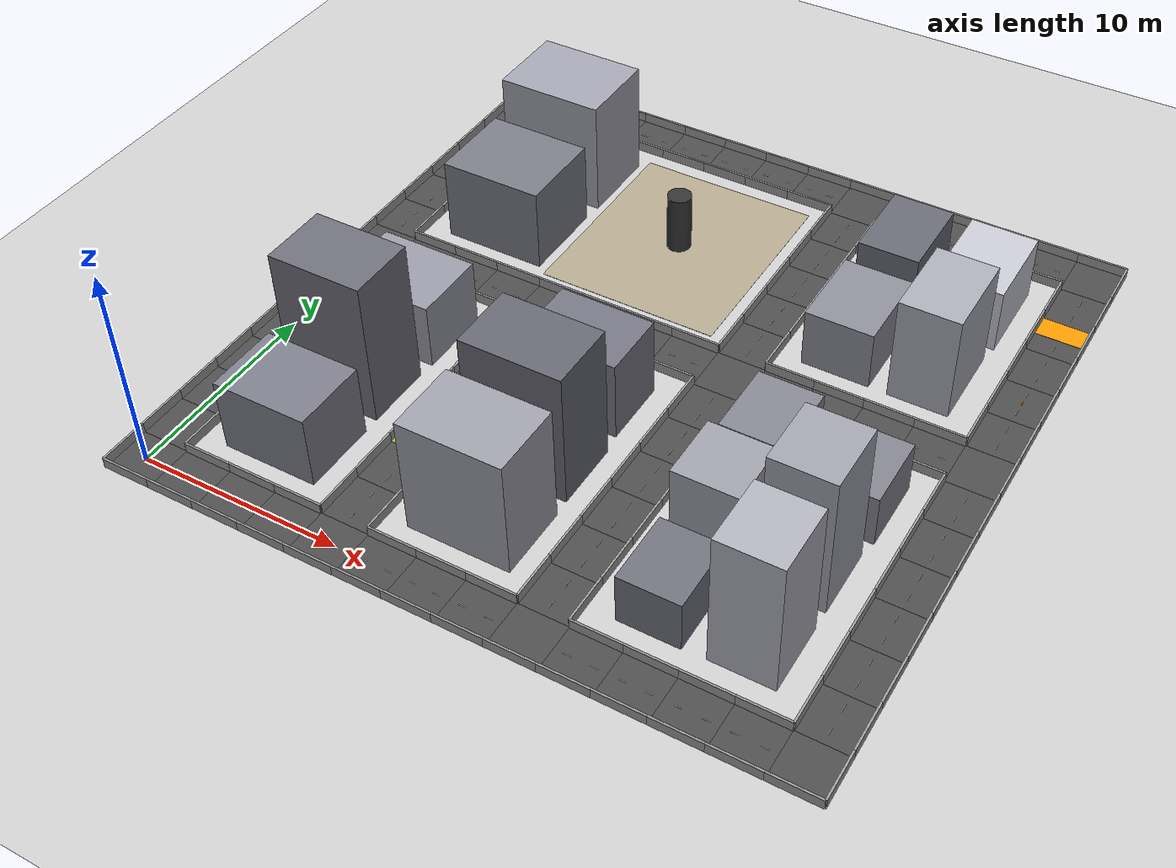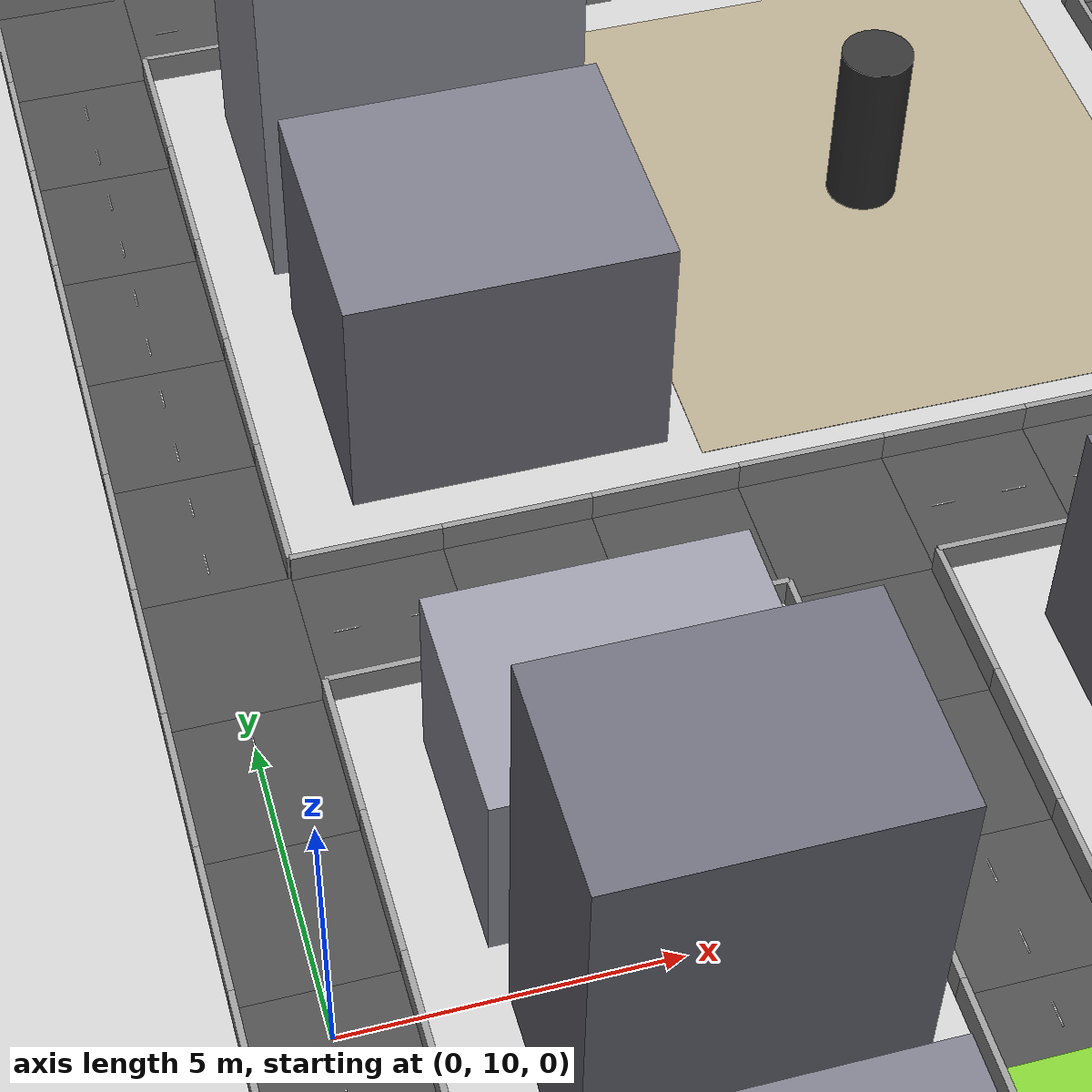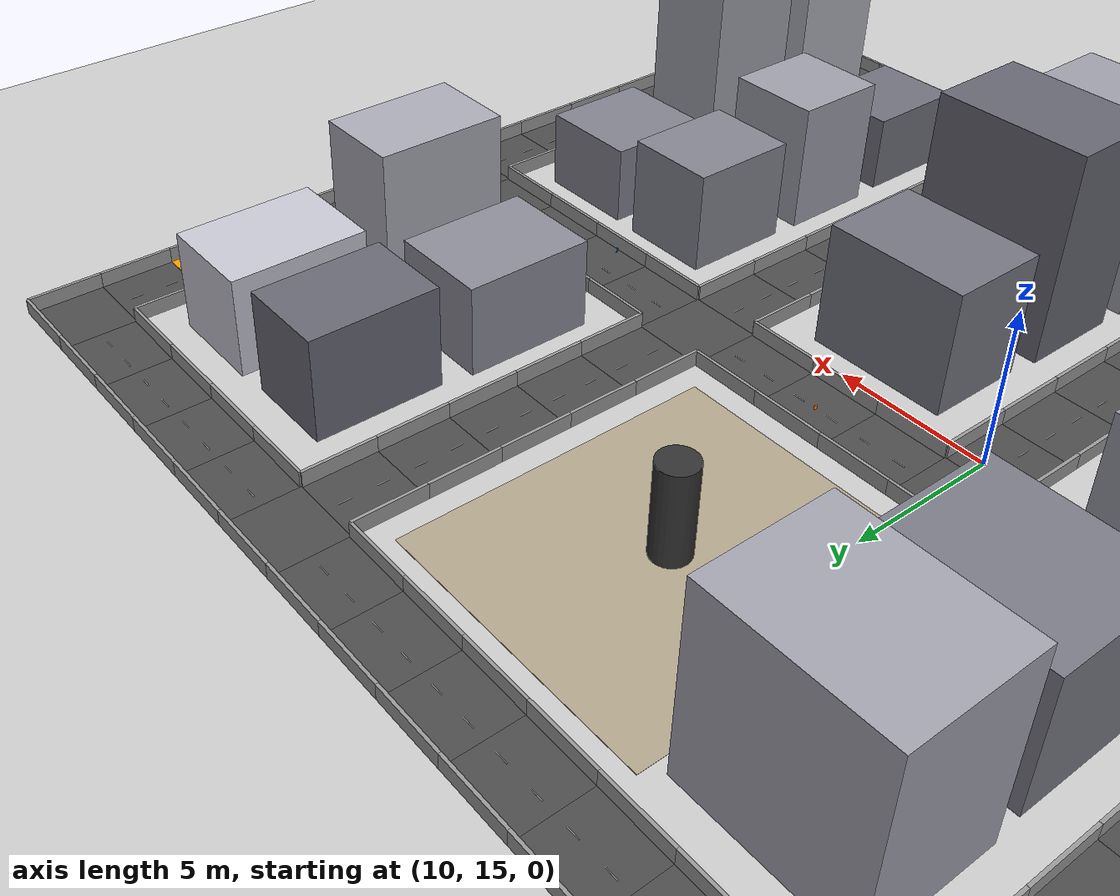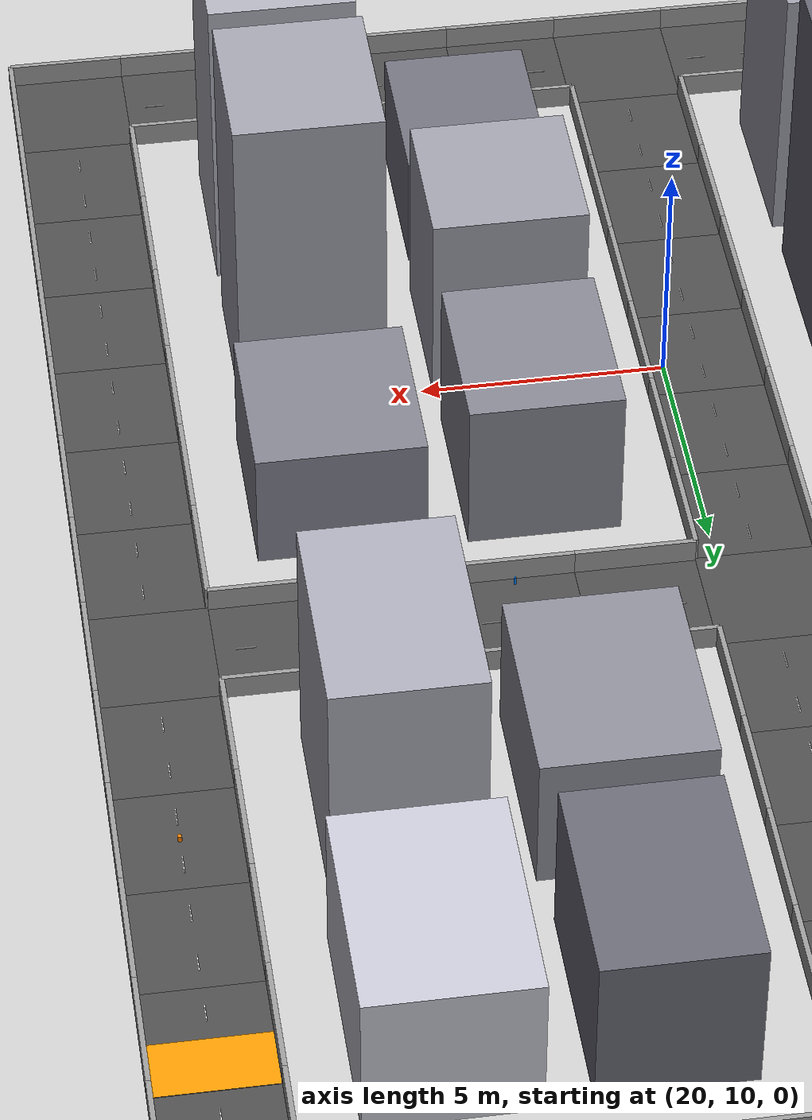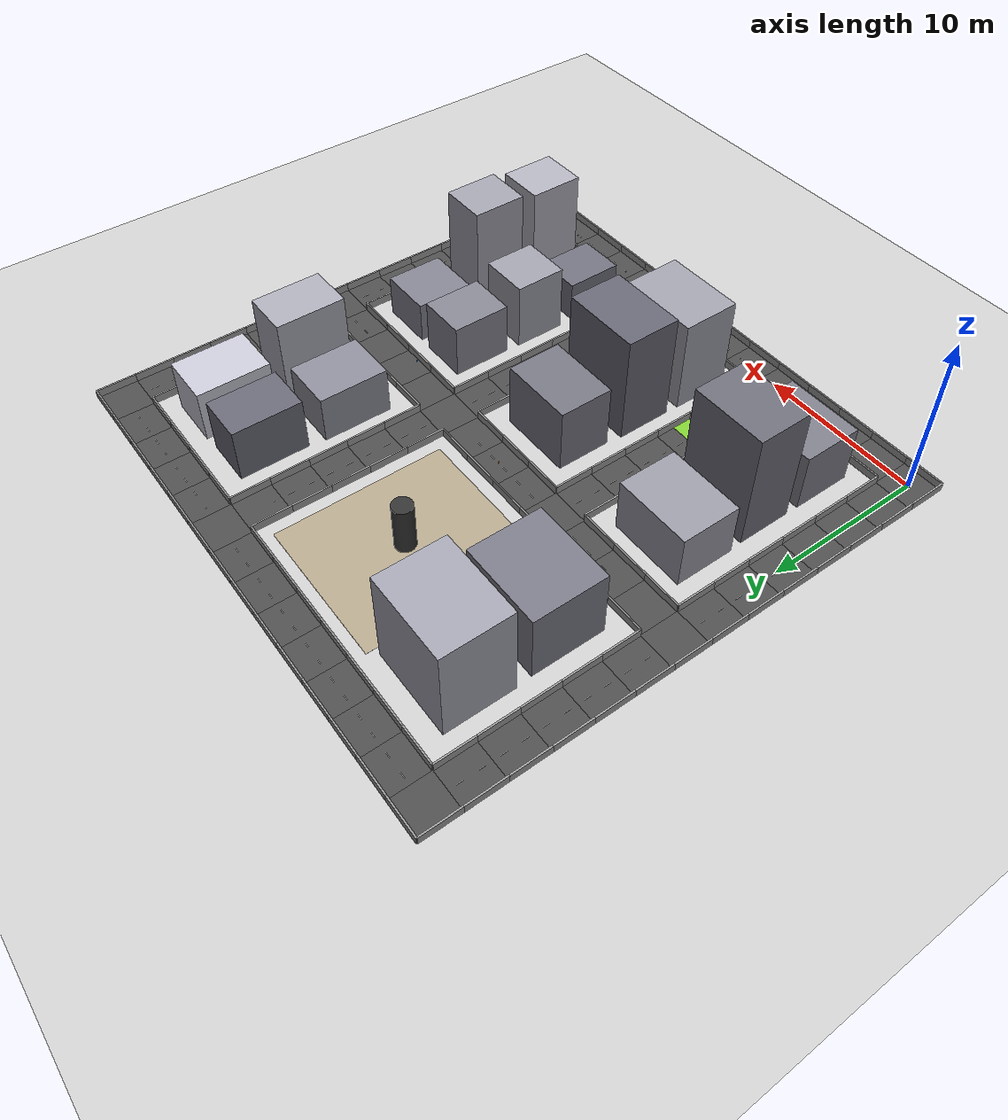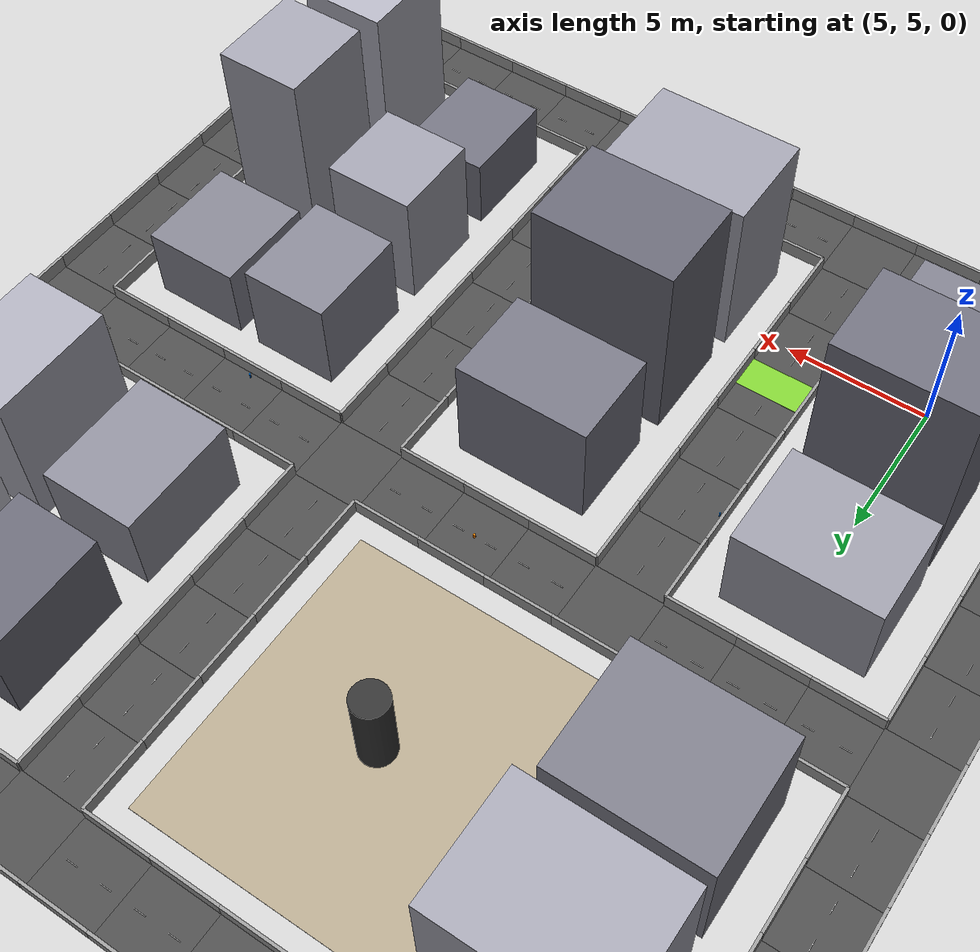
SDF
<?xml version="1.0" ?>
<sdf version="1.6">
  <world name="grid_city_base">
    <scene>
      <ambient>0.4 0.4 0.4 1</ambient>
      <background>0.7 0.7 0.7 1</background>
      <shadows>true</shadows>
    </scene>
    <physics type="ode">
      <max_step_size>0.001</max_step_size>
      <real_time_update_rate>10000</real_time_update_rate>
    </physics>
    <plugin name="gazebo_ros_state" filename="libgazebo_ros_state.so">
      <ros><namespace>/gazebo</namespace></ros>
    </plugin>
    <include><uri>model://sun</uri></include>
    <include><uri>model://ground_plane</uri></include>

    <model name="road_network">
      <static>true</static>
      <link name="link">
        <collision name="road_col_0"><pose>0.0 0.0 0 0 0 0</pose><geometry><box><size>2.4 2.4 0.01</size></box></geometry></collision>
        <visual name="road_vis_0"><pose>0.0 0.0 0 0 0 0</pose><geometry><box><size>2.4 2.4 0.01</size></box></geometry><material><ambient>0.3 0.3 0.3 1</ambient><diffuse>0.3 0.3 0.3 1</diffuse></material></visual>
        <collision name="wall_b_0"><pose>0.0 -1.2 0.25 0 0 0</pose><geometry><box><size>2.4 0.1 0.5</size></box></geometry></collision>
        <visual name="wall_bv_0"><pose>0.0 -1.2 0.25 0 0 0</pose><geometry><box><size>2.4 0.1 0.5</size></box></geometry><material><ambient>0.6 0.6 0.6 1</ambient></material></visual>
        <visual name="line_b_0"><pose>0.0 -1.18 0.006 0 0 0</pose><geometry><box><size>2.4 0.02 0.01</size></box></geometry><material><ambient>1 1 1 1</ambient></material></visual>
        <collision name="wall_l_0"><pose>-1.2 0.0 0.25 0 0 1.570796</pose><geometry><box><size>2.4 0.1 0.5</size></box></geometry></collision>
        <visual name="wall_lv_0"><pose>-1.2 0.0 0.25 0 0 1.570796</pose><geometry><box><size>2.4 0.1 0.5</size></box></geometry><material><ambient>0.6 0.6 0.6 1</ambient></material></visual>
        <visual name="line_l_0"><pose>-1.18 0.0 0.006 0 0 1.570796</pose><geometry><box><size>2.4 0.02 0.01</size></box></geometry><material><ambient>1 1 1 1</ambient></material></visual>
        <collision name="road_col_1"><pose>2.4 0.0 0 0 0 0</pose><geometry><box><size>2.4 2.4 0.01</size></box></geometry></collision>
        <visual name="road_vis_1"><pose>2.4 0.0 0 0 0 0</pose><geometry><box><size>2.4 2.4 0.01</size></box></geometry><material><ambient>0.3 0.3 0.3 1</ambient><diffuse>0.3 0.3 0.3 1</diffuse></material></visual>
        <collision name="wall_t_1"><pose>2.4 1.2 0.25 0 0 0</pose><geometry><box><size>2.4 0.1 0.5</size></box></geometry></collision>
        <visual name="wall_tv_1"><pose>2.4 1.2 0.25 0 0 0</pose><geometry><box><size>2.4 0.1 0.5</size></box></geometry><material><ambient>0.6 0.6 0.6 1</ambient></material></visual>
        <visual name="line_t_1"><pose>2.4 1.18 0.006 0 0 0</pose><geometry><box><size>2.4 0.02 0.01</size></box></geometry><material><ambient>1 1 1 1</ambient></material></visual>
        <collision name="wall_b_1"><pose>2.4 -1.2 0.25 0 0 0</pose><geometry><box><size>2.4 0.1 0.5</size></box></geometry></collision>
        <visual name="wall_bv_1"><pose>2.4 -1.2 0.25 0 0 0</pose><geometry><box><size>2.4 0.1 0.5</size></box></geometry><material><ambient>0.6 0.6 0.6 1</ambient></material></visual>
        <visual name="line_b_1"><pose>2.4 -1.18 0.006 0 0 0</pose><geometry><box><size>2.4 0.02 0.01</size></box></geometry><material><ambient>1 1 1 1</ambient></material></visual>
        <visual name="dash_h1_1"><pose>1.7999999999999998 0.0 0.006 0 0 0</pose><geometry><box><size>0.4 0.02 0.01</size></box></geometry><material><ambient>1 1 1 1</ambient></material></visual>
        <visual name="dash_h2_1"><pose>3.0 0.0 0.006 0 0 0</pose><geometry><box><size>0.4 0.02 0.01</size></box></geometry><material><ambient>1 1 1 1</ambient></material></visual>
        <collision name="road_col_2"><pose>4.8 0.0 0 0 0 0</pose><geometry><box><size>2.4 2.4 0.01</size></box></geometry></collision>
        <visual name="road_vis_2"><pose>4.8 0.0 0 0 0 0</pose><geometry><box><size>2.4 2.4 0.01</size></box></geometry><material><ambient>0.3 0.3 0.3 1</ambient><diffuse>0.3 0.3 0.3 1</diffuse></material></visual>
        <collision name="wall_t_2"><pose>4.8 1.2 0.25 0 0 0</pose><geometry><box><size>2.4 0.1 0.5</size></box></geometry></collision>
        <visual name="wall_tv_2"><pose>4.8 1.2 0.25 0 0 0</pose><geometry><box><size>2.4 0.1 0.5</size></box></geometry><material><ambient>0.6 0.6 0.6 1</ambient></material></visual>
        <visual name="line_t_2"><pose>4.8 1.18 0.006 0 0 0</pose><geometry><box><size>2.4 0.02 0.01</size></box></geometry><material><ambient>1 1 1 1</ambient></material></visual>
        <collision name="wall_b_2"><pose>4.8 -1.2 0.25 0 0 0</pose><geometry><box><size>2.4 0.1 0.5</size></box></geometry></collision>
        <visual name="wall_bv_2"><pose>4.8 -1.2 0.25 0 0 0</pose><geometry><box><size>2.4 0.1 0.5</size></box></geometry><material><ambient>0.6 0.6 0.6 1</ambient></material></visual>
        <visual name="line_b_2"><pose>4.8 -1.18 0.006 0 0 0</pose><geometry><box><size>2.4 0.02 0.01</size></box></geometry><material><ambient>1 1 1 1</ambient></material></visual>
        <visual name="dash_h1_2"><pose>4.2 0.0 0.006 0 0 0</pose><geometry><box><size>0.4 0.02 0.01</size></box></geometry><material><ambient>1 1 1 1</ambient></material></visual>
        <visual name="dash_h2_2"><pose>5.3999999999999995 0.0 0.006 0 0 0</pose><geometry><box><size>0.4 0.02 0.01</size></box></geometry><material><ambient>1 1 1 1</ambient></material></visual>
        <collision name="road_col_3"><pose>7.199999999999999 0.0 0 0 0 0</pose><geometry><box><size>2.4 2.4 0.01</size></box></geometry></collision>
        <visual name="road_vis_3"><pose>7.199999999999999 0.0 0 0 0 0</pose><geometry><box><size>2.4 2.4 0.01</size></box></geometry><material><ambient>0.3 0.3 0.3 1</ambient><diffuse>0.3 0.3 0.3 1</diffuse></material></visual>
        <collision name="wall_t_3"><pose>7.199999999999999 1.2 0.25 0 0 0</pose><geometry><box><size>2.4 0.1 0.5</size></box></geometry></collision>
        <visual name="wall_tv_3"><pose>7.199999999999999 1.2 0.25 0 0 0</pose><geometry><box><size>2.4 0.1 0.5</size></box></geometry><material><ambient>0.6 0.6 0.6 1</ambient></material></visual>
        <visual name="line_t_3"><pose>7.199999999999999 1.18 0.006 0 0 0</pose><geometry><box><size>2.4 0.02 0.01</size></box></geometry><material><ambient>1 1 1 1</ambient></material></visual>
        <collision name="wall_b_3"><pose>7.199999999999999 -1.2 0.25 0 0 0</pose><geometry><box><size>2.4 0.1 0.5</size></box></geometry></collision>
        <visual name="wall_bv_3"><pose>7.199999999999999 -1.2 0.25 0 0 0</pose><geometry><box><size>2.4 0.1 0.5</size></box></geometry><material><ambient>0.6 0.6 0.6 1</ambient></material></visual>
        <visual name="line_b_3"><pose>7.199999999999999 -1.18 0.006 0 0 0</pose><geometry><box><size>2.4 0.02 0.01</size></box></geometry><material><ambient>1 1 1 1</ambient></material></visual>
        <visual name="dash_h1_3"><pose>6.6 0.0 0.006 0 0 0</pose><geometry><box><size>0.4 0.02 0.01</size></box></geometry><material><ambient>1 1 1 1</ambient></material></visual>
        <visual name="dash_h2_3"><pose>7.799999999999999 0.0 0.006 0 0 0</pose><geometry><box><size>0.4 0.02 0.01</size></box></geometry><material><ambient>1 1 1 1</ambient></material></visual>
        <collision name="road_col_4"><pose>9.6 0.0 0 0 0 0</pose><geometry><box><size>2.4 2.4 0.01</size></box></geometry></collision>
        <visual name="road_vis_4"><pose>9.6 0.0 0 0 0 0</pose><geometry><box><size>2.4 2.4 0.01</size></box></geometry><material><ambient>0.3 0.3 0.3 1</ambient><diffuse>0.3 0.3 0.3 1</diffuse></material></visual>
        <collision name="wall_b_4"><pose>9.6 -1.2 0.25 0 0 0</pose><geometry><box><size>2.4 0.1 0.5</size></box></geometry></collision>
        <visual name="wall_bv_4"><pose>9.6 -1.2 0.25 0 0 0</pose><geometry><box><size>2.4 0.1 0.5</size></box></geometry><material><ambient>0.6 0.6 0.6 1</ambient></material></visual>
        <visual name="line_b_4"><pose>9.6 -1.18 0.006 0 0 0</pose><geometry><box><size>2.4 0.02 0.01</size></box></geometry><material><ambient>1 1 1 1</ambient></material></visual>
        <collision name="road_col_5"><pose>12.0 0.0 0 0 0 0</pose><geometry><box><size>2.4 2.4 0.01</size></box></geometry></collision>
        <visual name="road_vis_5"><pose>12.0 0.0 0 0 0 0</pose><geometry><box><size>2.4 2.4 0.01</size></box></geometry><material><ambient>0.3 0.3 0.3 1</ambient><diffuse>0.3 0.3 0.3 1</diffuse></material></visual>
        <collision name="wall_t_5"><pose>12.0 1.2 0.25 0 0 0</pose><geometry><box><size>2.4 0.1 0.5</size></box></geometry></collision>
        <visual name="wall_tv_5"><pose>12.0 1.2 0.25 0 0 0</pose><geometry><box><size>2.4 0.1 0.5</size></box></geometry><material><ambient>0.6 0.6 0.6 1</ambient></material></visual>
        <visual name="line_t_5"><pose>12.0 1.18 0.006 0 0 0</pose><geometry><box><size>2.4 0.02 0.01</size></box></geometry><material><ambient>1 1 1 1</ambient></material></visual>
        <collision name="wall_b_5"><pose>12.0 -1.2 0.25 0 0 0</pose><geometry><box><size>2.4 0.1 0.5</size></box></geometry></collision>
        <visual name="wall_bv_5"><pose>12.0 -1.2 0.25 0 0 0</pose><geometry><box><size>2.4 0.1 0.5</size></box></geometry><material><ambient>0.6 0.6 0.6 1</ambient></material></visual>
        <visual name="line_b_5"><pose>12.0 -1.18 0.006 0 0 0</pose><geometry><box><size>2.4 0.02 0.01</size></box></geometry><material><ambient>1 1 1 1</ambient></material></visual>
        <visual name="dash_h1_5"><pose>11.4 0.0 0.006 0 0 0</pose><geometry><box><size>0.4 0.02 0.01</size></box></geometry><material><ambient>1 1 1 1</ambient></material></visual>
        <visual name="dash_h2_5"><pose>12.6 0.0 0.006 0 0 0</pose><geometry><box><size>0.4 0.02 0.01</size></box></geometry><material><ambient>1 1 1 1</ambient></material></visual>
        <collision name="road_col_6"><pose>14.399999999999999 0.0 0 0 0 0</pose><geometry><box><size>2.4 2.4 0.01</size></box></geometry></collision>
        <visual name="road_vis_6"><pose>14.399999999999999 0.0 0 0 0 0</pose><geometry><box><size>2.4 2.4 0.01</size></box></geometry><material><ambient>0.3 0.3 0.3 1</ambient><diffuse>0.3 0.3 0.3 1</diffuse></material></visual>
        <collision name="wall_t_6"><pose>14.399999999999999 1.2 0.25 0 0 0</pose><geometry><box><size>2.4 0.1 0.5</size></box></geometry></collision>
        <visual name="wall_tv_6"><pose>14.399999999999999 1.2 0.25 0 0 0</pose><geometry><box><size>2.4 0.1 0.5</size></box></geometry><material><ambient>0.6 0.6 0.6 1</ambient></material></visual>
        <visual name="line_t_6"><pose>14.399999999999999 1.18 0.006 0 0 0</pose><geometry><box><size>2.4 0.02 0.01</size></box></geometry><material><ambient>1 1 1 1</ambient></material></visual>
        <collision name="wall_b_6"><pose>14.399999999999999 -1.2 0.25 0 0 0</pose><geometry><box><size>2.4 0.1 0.5</size></box></geometry></collision>
        <visual name="wall_bv_6"><pose>14.399999999999999 -1.2 0.25 0 0 0</pose><geometry><box><size>2.4 0.1 0.5</size></box></geometry><material><ambient>0.6 0.6 0.6 1</ambient></material></visual>
        <visual name="line_b_6"><pose>14.399999999999999 -1.18 0.006 0 0 0</pose><geometry><box><size>2.4 0.02 0.01</size></box></geometry><material><ambient>1 1 1 1</ambient></material></visual>
        <visual name="dash_h1_6"><pose>13.799999999999999 0.0 0.006 0 0 0</pose><geometry><box><size>0.4 0.02 0.01</size></box></geometry><material><ambient>1 1 1 1</ambient></material></visual>
        <visual name="dash_h2_6"><pose>14.999999999999998 0.0 0.006 0 0 0</pose><geometry><box><size>0.4 0.02 0.01</size></box></geometry><material><ambient>1 1 1 1</ambient></material></visual>
        <collision name="road_col_7"><pose>16.8 0.0 0 0 0 0</pose><geometry><box><size>2.4 2.4 0.01</size></box></geometry></collision>
        <visual name="road_vis_7"><pose>16.8 0.0 0 0 0 0</pose><geometry><box><size>2.4 2.4 0.01</size></box></geometry><material><ambient>0.3 0.3 0.3 1</ambient><diffuse>0.3 0.3 0.3 1</diffuse></material></visual>
        <collision name="wall_t_7"><pose>16.8 1.2 0.25 0 0 0</pose><geometry><box><size>2.4 0.1 0.5</size></box></geometry></collision>
        <visual name="wall_tv_7"><pose>16.8 1.2 0.25 0 0 0</pose><geometry><box><size>2.4 0.1 0.5</size></box></geometry><material><ambient>0.6 0.6 0.6 1</ambient></material></visual>
        <visual name="line_t_7"><pose>16.8 1.18 0.006 0 0 0</pose><geometry><box><size>2.4 0.02 0.01</size></box></geometry><material><ambient>1 1 1 1</ambient></material></visual>
        <collision name="wall_b_7"><pose>16.8 -1.2 0.25 0 0 0</pose><geometry><box><size>2.4 0.1 0.5</size></box></geometry></collision>
        <visual name="wall_bv_7"><pose>16.8 -1.2 0.25 0 0 0</pose><geometry><box><size>2.4 0.1 0.5</size></box></geometry><material><ambient>0.6 0.6 0.6 1</ambient></material></visual>
        <visual name="line_b_7"><pose>16.8 -1.18 0.006 0 0 0</pose><geometry><box><size>2.4 0.02 0.01</size></box></geometry><material><ambient>1 1 1 1</ambient></material></visual>
        <visual name="dash_h1_7"><pose>16.2 0.0 0.006 0 0 0</pose><geometry><box><size>0.4 0.02 0.01</size></box></geometry><material><ambient>1 1 1 1</ambient></material></visual>
        <visual name="dash_h2_7"><pose>17.400000000000002 0.0 0.006 0 0 0</pose><geometry><box><size>0.4 0.02 0.01</size></box></geometry><material><ambient>1 1 1 1</ambient></material></visual>
        <collision name="road_col_8"><pose>19.2 0.0 0 0 0 0</pose><geometry><box><size>2.4 2.4 0.01</size></box></geometry></collision>
        <visual name="road_vis_8"><pose>19.2 0.0 0 0 0 0</pose><geometry><box><size>2.4 2.4 0.01</size></box></geometry><material><ambient>0.3 0.3 0.3 1</ambient><diffuse>0.3 0.3 0.3 1</diffuse></material></visual>
        <collision name="wall_b_8"><pose>19.2 -1.2 0.25 0 0 0</pose><geometry><box><size>2.4 0.1 0.5</size></box></geometry></collision>
        <visual name="wall_bv_8"><pose>19.2 -1.2 0.25 0 0 0</pose><geometry><box><size>2.4 0.1 0.5</size></box></geometry><material><ambient>0.6 0.6 0.6 1</ambient></material></visual>
        <visual name="line_b_8"><pose>19.2 -1.18 0.006 0 0 0</pose><geometry><box><size>2.4 0.02 0.01</size></box></geometry><material><ambient>1 1 1 1</ambient></material></visual>
        <collision name="road_col_9"><pose>21.599999999999998 0.0 0 0 0 0</pose><geometry><box><size>2.4 2.4 0.01</size></box></geometry></collision>
        <visual name="road_vis_9"><pose>21.599999999999998 0.0 0 0 0 0</pose><geometry><box><size>2.4 2.4 0.01</size></box></geometry><material><ambient>0.3 0.3 0.3 1</ambient><diffuse>0.3 0.3 0.3 1</diffuse></material></visual>
        <collision name="wall_t_9"><pose>21.599999999999998 1.2 0.25 0 0 0</pose><geometry><box><size>2.4 0.1 0.5</size></box></geometry></collision>
        <visual name="wall_tv_9"><pose>21.599999999999998 1.2 0.25 0 0 0</pose><geometry><box><size>2.4 0.1 0.5</size></box></geometry><material><ambient>0.6 0.6 0.6 1</ambient></material></visual>
        <visual name="line_t_9"><pose>21.599999999999998 1.18 0.006 0 0 0</pose><geometry><box><size>2.4 0.02 0.01</size></box></geometry><material><ambient>1 1 1 1</ambient></material></visual>
        <collision name="wall_b_9"><pose>21.599999999999998 -1.2 0.25 0 0 0</pose><geometry><box><size>2.4 0.1 0.5</size></box></geometry></collision>
        <visual name="wall_bv_9"><pose>21.599999999999998 -1.2 0.25 0 0 0</pose><geometry><box><size>2.4 0.1 0.5</size></box></geometry><material><ambient>0.6 0.6 0.6 1</ambient></material></visual>
        <visual name="line_b_9"><pose>21.599999999999998 -1.18 0.006 0 0 0</pose><geometry><box><size>2.4 0.02 0.01</size></box></geometry><material><ambient>1 1 1 1</ambient></material></visual>
        <visual name="dash_h1_9"><pose>20.999999999999996 0.0 0.006 0 0 0</pose><geometry><box><size>0.4 0.02 0.01</size></box></geometry><material><ambient>1 1 1 1</ambient></material></visual>
        <visual name="dash_h2_9"><pose>22.2 0.0 0.006 0 0 0</pose><geometry><box><size>0.4 0.02 0.01</size></box></geometry><material><ambient>1 1 1 1</ambient></material></visual>
        <collision name="road_col_10"><pose>24.0 0.0 0 0 0 0</pose><geometry><box><size>2.4 2.4 0.01</size></box></geometry></collision>
        <visual name="road_vis_10"><pose>24.0 0.0 0 0 0 0</pose><geometry><box><size>2.4 2.4 0.01</size></box></geometry><material><ambient>0.3 0.3 0.3 1</ambient><diffuse>0.3 0.3 0.3 1</diffuse></material></visual>
        <collision name="wall_t_10"><pose>24.0 1.2 0.25 0 0 0</pose><geometry><box><size>2.4 0.1 0.5</size></box></geometry></collision>
        <visual name="wall_tv_10"><pose>24.0 1.2 0.25 0 0 0</pose><geometry><box><size>2.4 0.1 0.5</size></box></geometry><material><ambient>0.6 0.6 0.6 1</ambient></material></visual>
        <visual name="line_t_10"><pose>24.0 1.18 0.006 0 0 0</pose><geometry><box><size>2.4 0.02 0.01</size></box></geometry><material><ambient>1 1 1 1</ambient></material></visual>
        <collision name="wall_b_10"><pose>24.0 -1.2 0.25 0 0 0</pose><geometry><box><size>2.4 0.1 0.5</size></box></geometry></collision>
        <visual name="wall_bv_10"><pose>24.0 -1.2 0.25 0 0 0</pose><geometry><box><size>2.4 0.1 0.5</size></box></geometry><material><ambient>0.6 0.6 0.6 1</ambient></material></visual>
        <visual name="line_b_10"><pose>24.0 -1.18 0.006 0 0 0</pose><geometry><box><size>2.4 0.02 0.01</size></box></geometry><material><ambient>1 1 1 1</ambient></material></visual>
        <visual name="dash_h1_10"><pose>23.4 0.0 0.006 0 0 0</pose><geometry><box><size>0.4 0.02 0.01</size></box></geometry><material><ambient>1 1 1 1</ambient></material></visual>
        <visual name="dash_h2_10"><pose>24.6 0.0 0.006 0 0 0</pose><geometry><box><size>0.4 0.02 0.01</size></box></geometry><material><ambient>1 1 1 1</ambient></material></visual>
        <collision name="road_col_11"><pose>26.4 0.0 0 0 0 0</pose><geometry><box><size>2.4 2.4 0.01</size></box></geometry></collision>
        <visual name="road_vis_11"><pose>26.4 0.0 0 0 0 0</pose><geometry><box><size>2.4 2.4 0.01</size></box></geometry><material><ambient>0.3 0.3 0.3 1</ambient><diffuse>0.3 0.3 0.3 1</diffuse></material></visual>
        <collision name="wall_t_11"><pose>26.4 1.2 0.25 0 0 0</pose><geometry><box><size>2.4 0.1 0.5</size></box></geometry></collision>
        <visual name="wall_tv_11"><pose>26.4 1.2 0.25 0 0 0</pose><geometry><box><size>2.4 0.1 0.5</size></box></geometry><material><ambient>0.6 0.6 0.6 1</ambient></material></visual>
        <visual name="line_t_11"><pose>26.4 1.18 0.006 0 0 0</pose><geometry><box><size>2.4 0.02 0.01</size></box></geometry><material><ambient>1 1 1 1</ambient></material></visual>
        <collision name="wall_b_11"><pose>26.4 -1.2 0.25 0 0 0</pose><geometry><box><size>2.4 0.1 0.5</size></box></geometry></collision>
        <visual name="wall_bv_11"><pose>26.4 -1.2 0.25 0 0 0</pose><geometry><box><size>2.4 0.1 0.5</size></box></geometry><material><ambient>0.6 0.6 0.6 1</ambient></material></visual>
        <visual name="line_b_11"><pose>26.4 -1.18 0.006 0 0 0</pose><geometry><box><size>2.4 0.02 0.01</size></box></geometry><material><ambient>1 1 1 1</ambient></material></visual>
        <visual name="dash_h1_11"><pose>25.799999999999997 0.0 0.006 0 0 0</pose><geometry><box><size>0.4 0.02 0.01</size></box></geometry><material><ambient>1 1 1 1</ambient></material></visual>
        <visual name="dash_h2_11"><pose>27.0 0.0 0.006 0 0 0</pose><geometry><box><size>0.4 0.02 0.01</size></box></geometry><material><ambient>1 1 1 1</ambient></material></visual>
        <collision name="road_col_12"><pose>28.799999999999997 0.0 0 0 0 0</pose><geometry><box><size>2.4 2.4 0.01</size></box></geometry></collision>
        <visual name="road_vis_12"><pose>28.799999999999997 0.0 0 0 0 0</pose><geometry><box><size>2.4 2.4 0.01</size></box></geometry><material><ambient>0.3 0.3 0.3 1</ambient><diffuse>0.3 0.3 0.3 1</diffuse></material></visual>
        <collision name="wall_t_12"><pose>28.799999999999997 1.2 0.25 0 0 0</pose><geometry><box><size>2.4 0.1 0.5</size></box></geometry></collision>
        <visual name="wall_tv_12"><pose>28.799999999999997 1.2 0.25 0 0 0</pose><geometry><box><size>2.4 0.1 0.5</size></box></geometry><material><ambient>0.6 0.6 0.6 1</ambient></material></visual>
        <visual name="line_t_12"><pose>28.799999999999997 1.18 0.006 0 0 0</pose><geometry><box><size>2.4 0.02 0.01</size></box></geometry><material><ambient>1 1 1 1</ambient></material></visual>
        <collision name="wall_b_12"><pose>28.799999999999997 -1.2 0.25 0 0 0</pose><geometry><box><size>2.4 0.1 0.5</size></box></geometry></collision>
        <visual name="wall_bv_12"><pose>28.799999999999997 -1.2 0.25 0 0 0</pose><geometry><box><size>2.4 0.1 0.5</size></box></geometry><material><ambient>0.6 0.6 0.6 1</ambient></material></visual>
        <visual name="line_b_12"><pose>28.799999999999997 -1.18 0.006 0 0 0</pose><geometry><box><size>2.4 0.02 0.01</size></box></geometry><material><ambient>1 1 1 1</ambient></material></visual>
        <visual name="dash_h1_12"><pose>28.199999999999996 0.0 0.006 0 0 0</pose><geometry><box><size>0.4 0.02 0.01</size></box></geometry><material><ambient>1 1 1 1</ambient></material></visual>
        <visual name="dash_h2_12"><pose>29.4 0.0 0.006 0 0 0</pose><geometry><box><size>0.4 0.02 0.01</size></box></geometry><material><ambient>1 1 1 1</ambient></material></visual>
        <collision name="road_col_13"><pose>31.2 0.0 0 0 0 0</pose><geometry><box><size>2.4 2.4 0.01</size></box></geometry></collision>
        <visual name="road_vis_13"><pose>31.2 0.0 0 0 0 0</pose><geometry><box><size>2.4 2.4 0.01</size></box></geometry><material><ambient>0.3 0.3 0.3 1</ambient><diffuse>0.3 0.3 0.3 1</diffuse></material></visual>
        <collision name="wall_b_13"><pose>31.2 -1.2 0.25 0 0 0</pose><geometry><box><size>2.4 0.1 0.5</size></box></geometry></collision>
        <visual name="wall_bv_13"><pose>31.2 -1.2 0.25 0 0 0</pose><geometry><box><size>2.4 0.1 0.5</size></box></geometry><material><ambient>0.6 0.6 0.6 1</ambient></material></visual>
        <visual name="line_b_13"><pose>31.2 -1.18 0.006 0 0 0</pose><geometry><box><size>2.4 0.02 0.01</size></box></geometry><material><ambient>1 1 1 1</ambient></material></visual>
        <collision name="wall_r_13"><pose>32.4 0.0 0.25 0 0 1.570796</pose><geometry><box><size>2.4 0.1 0.5</size></box></geometry></collision>
        <visual name="wall_rv_13"><pose>32.4 0.0 0.25 0 0 1.570796</pose><geometry><box><size>2.4 0.1 0.5</size></box></geometry><material><ambient>0.6 0.6 0.6 1</ambient></material></visual>
        <visual name="line_r_13"><pose>32.38 0.0 0.006 0 0 1.570796</pose><geometry><box><size>2.4 0.02 0.01</size></box></geometry><material><ambient>1 1 1 1</ambient></material></visual>
        <collision name="road_col_14"><pose>0.0 2.4 0 0 0 0</pose><geometry><box><size>2.4 2.4 0.01</size></box></geometry></collision>
        <visual name="road_vis_14"><pose>0.0 2.4 0 0 0 0</pose><geometry><box><size>2.4 2.4 0.01</size></box></geometry><material><ambient>0.3 0.3 0.3 1</ambient><diffuse>0.3 0.3 0.3 1</diffuse></material></visual>
        <collision name="wall_r_14"><pose>1.2 2.4 0.25 0 0 1.570796</pose><geometry><box><size>2.4 0.1 0.5</size></box></geometry></collision>
        <visual name="wall_rv_14"><pose>1.2 2.4 0.25 0 0 1.570796</pose><geometry><box><size>2.4 0.1 0.5</size></box></geometry><material><ambient>0.6 0.6 0.6 1</ambient></material></visual>
        <visual name="line_r_14"><pose>1.18 2.4 0.006 0 0 1.570796</pose><geometry><box><size>2.4 0.02 0.01</size></box></geometry><material><ambient>1 1 1 1</ambient></material></visual>
        <collision name="wall_l_14"><pose>-1.2 2.4 0.25 0 0 1.570796</pose><geometry><box><size>2.4 0.1 0.5</size></box></geometry></collision>
        <visual name="wall_lv_14"><pose>-1.2 2.4 0.25 0 0 1.570796</pose><geometry><box><size>2.4 0.1 0.5</size></box></geometry><material><ambient>0.6 0.6 0.6 1</ambient></material></visual>
        <visual name="line_l_14"><pose>-1.18 2.4 0.006 0 0 1.570796</pose><geometry><box><size>2.4 0.02 0.01</size></box></geometry><material><ambient>1 1 1 1</ambient></material></visual>
        <visual name="dash_v1_14"><pose>0.0 1.7999999999999998 0.006 0 0 1.570796</pose><geometry><box><size>0.4 0.02 0.01</size></box></geometry><material><ambient>1 1 1 1</ambient></material></visual>
        <visual name="dash_v2_14"><pose>0.0 3.0 0.006 0 0 1.570796</pose><geometry><box><size>0.4 0.02 0.01</size></box></geometry><material><ambient>1 1 1 1</ambient></material></visual>
        <collision name="road_col_15"><pose>9.6 2.4 0 0 0 0</pose><geometry><box><size>2.4 2.4 0.01</size></box></geometry></collision>
        <visual name="road_vis_15"><pose>9.6 2.4 0 0 0 0</pose><geometry><box><size>2.4 2.4 0.01</size></box></geometry><material><ambient>0.3 0.3 0.3 1</ambient><diffuse>0.3 0.3 0.3 1</diffuse></material></visual>
        <collision name="wall_r_15"><pose>10.799999999999999 2.4 0.25 0 0 1.570796</pose><geometry><box><size>2.4 0.1 0.5</size></box></geometry></collision>
        <visual name="wall_rv_15"><pose>10.799999999999999 2.4 0.25 0 0 1.570796</pose><geometry><box><size>2.4 0.1 0.5</size></box></geometry><material><ambient>0.6 0.6 0.6 1</ambient></material></visual>
        <visual name="line_r_15"><pose>10.78 2.4 0.006 0 0 1.570796</pose><geometry><box><size>2.4 0.02 0.01</size></box></geometry><material><ambient>1 1 1 1</ambient></material></visual>
        <collision name="wall_l_15"><pose>8.4 2.4 0.25 0 0 1.570796</pose><geometry><box><size>2.4 0.1 0.5</size></box></geometry></collision>
        <visual name="wall_lv_15"><pose>8.4 2.4 0.25 0 0 1.570796</pose><geometry><box><size>2.4 0.1 0.5</size></box></geometry><material><ambient>0.6 0.6 0.6 1</ambient></material></visual>
        <visual name="line_l_15"><pose>8.42 2.4 0.006 0 0 1.570796</pose><geometry><box><size>2.4 0.02 0.01</size></box></geometry><material><ambient>1 1 1 1</ambient></material></visual>
        <visual name="dash_v1_15"><pose>9.6 1.7999999999999998 0.006 0 0 1.570796</pose><geometry><box><size>0.4 0.02 0.01</size></box></geometry><material><ambient>1 1 1 1</ambient></material></visual>
        <visual name="dash_v2_15"><pose>9.6 3.0 0.006 0 0 1.570796</pose><geometry><box><size>0.4 0.02 0.01</size></box></geometry><material><ambient>1 1 1 1</ambient></material></visual>
        <collision name="road_col_16"><pose>19.2 2.4 0 0 0 0</pose><geometry><box><size>2.4 2.4 0.01</size></box></geometry></collision>
        <visual name="road_vis_16"><pose>19.2 2.4 0 0 0 0</pose><geometry><box><size>2.4 2.4 0.01</size></box></geometry><material><ambient>0.3 0.3 0.3 1</ambient><diffuse>0.3 0.3 0.3 1</diffuse></material></visual>
        <collision name="wall_r_16"><pose>20.4 2.4 0.25 0 0 1.570796</pose><geometry><box><size>2.4 0.1 0.5</size></box></geometry></collision>
        <visual name="wall_rv_16"><pose>20.4 2.4 0.25 0 0 1.570796</pose><geometry><box><size>2.4 0.1 0.5</size></box></geometry><material><ambient>0.6 0.6 0.6 1</ambient></material></visual>
        <visual name="line_r_16"><pose>20.38 2.4 0.006 0 0 1.570796</pose><geometry><box><size>2.4 0.02 0.01</size></box></geometry><material><ambient>1 1 1 1</ambient></material></visual>
        <collision name="wall_l_16"><pose>18.0 2.4 0.25 0 0 1.570796</pose><geometry><box><size>2.4 0.1 0.5</size></box></geometry></collision>
        <visual name="wall_lv_16"><pose>18.0 2.4 0.25 0 0 1.570796</pose><geometry><box><size>2.4 0.1 0.5</size></box></geometry><material><ambient>0.6 0.6 0.6 1</ambient></material></visual>
        <visual name="line_l_16"><pose>18.02 2.4 0.006 0 0 1.570796</pose><geometry><box><size>2.4 0.02 0.01</size></box></geometry><material><ambient>1 1 1 1</ambient></material></visual>
        <visual name="dash_v1_16"><pose>19.2 1.7999999999999998 0.006 0 0 1.570796</pose><geometry><box><size>0.4 0.02 0.01</size></box></geometry><material><ambient>1 1 1 1</ambient></material></visual>
        <visual name="dash_v2_16"><pose>19.2 3.0 0.006 0 0 1.570796</pose><geometry><box><size>0.4 0.02 0.01</size></box></geometry><material><ambient>1 1 1 1</ambient></material></visual>
        <collision name="road_col_17"><pose>31.2 2.4 0 0 0 0</pose><geometry><box><size>2.4 2.4 0.01</size></box></geometry></collision>
        <visual name="road_vis_17"><pose>31.2 2.4 0 0 0 0</pose><geometry><box><size>2.4 2.4 0.01</size></box></geometry><material><ambient>0.3 0.3 0.3 1</ambient><diffuse>0.3 0.3 0.3 1</diffuse></material></visual>
        <collision name="wall_r_17"><pose>32.4 2.4 0.25 0 0 1.570796</pose><geometry><box><size>2.4 0.1 0.5</size></box></geometry></collision>
        <visual name="wall_rv_17"><pose>32.4 2.4 0.25 0 0 1.570796</pose><geometry><box><size>2.4 0.1 0.5</size></box></geometry><material><ambient>0.6 0.6 0.6 1</ambient></material></visual>
        <visual name="line_r_17"><pose>32.38 2.4 0.006 0 0 1.570796</pose><geometry><box><size>2.4 0.02 0.01</size></box></geometry><material><ambient>1 1 1 1</ambient></material></visual>
        <collision name="wall_l_17"><pose>30.0 2.4 0.25 0 0 1.570796</pose><geometry><box><size>2.4 0.1 0.5</size></box></geometry></collision>
        <visual name="wall_lv_17"><pose>30.0 2.4 0.25 0 0 1.570796</pose><geometry><box><size>2.4 0.1 0.5</size></box></geometry><material><ambient>0.6 0.6 0.6 1</ambient></material></visual>
        <visual name="line_l_17"><pose>30.02 2.4 0.006 0 0 1.570796</pose><geometry><box><size>2.4 0.02 0.01</size></box></geometry><material><ambient>1 1 1 1</ambient></material></visual>
        <visual name="dash_v1_17"><pose>31.2 1.7999999999999998 0.006 0 0 1.570796</pose><geometry><box><size>0.4 0.02 0.01</size></box></geometry><material><ambient>1 1 1 1</ambient></material></visual>
        <visual name="dash_v2_17"><pose>31.2 3.0 0.006 0 0 1.570796</pose><geometry><box><size>0.4 0.02 0.01</size></box></geometry><material><ambient>1 1 1 1</ambient></material></visual>
        <collision name="road_col_18"><pose>0.0 4.8 0 0 0 0</pose><geometry><box><size>2.4 2.4 0.01</size></box></geometry></collision>
        <visual name="road_vis_18"><pose>0.0 4.8 0 0 0 0</pose><geometry><box><size>2.4 2.4 0.01</size></box></geometry><material><ambient>0.3 0.3 0.3 1</ambient><diffuse>0.3 0.3 0.3 1</diffuse></material></visual>
        <collision name="wall_r_18"><pose>1.2 4.8 0.25 0 0 1.570796</pose><geometry><box><size>2.4 0.1 0.5</size></box></geometry></collision>
        <visual name="wall_rv_18"><pose>1.2 4.8 0.25 0 0 1.570796</pose><geometry><box><size>2.4 0.1 0.5</size></box></geometry><material><ambient>0.6 0.6 0.6 1</ambient></material></visual>
        <visual name="line_r_18"><pose>1.18 4.8 0.006 0 0 1.570796</pose><geometry><box><size>2.4 0.02 0.01</size></box></geometry><material><ambient>1 1 1 1</ambient></material></visual>
        <collision name="wall_l_18"><pose>-1.2 4.8 0.25 0 0 1.570796</pose><geometry><box><size>2.4 0.1 0.5</size></box></geometry></collision>
        <visual name="wall_lv_18"><pose>-1.2 4.8 0.25 0 0 1.570796</pose><geometry><box><size>2.4 0.1 0.5</size></box></geometry><material><ambient>0.6 0.6 0.6 1</ambient></material></visual>
        <visual name="line_l_18"><pose>-1.18 4.8 0.006 0 0 1.570796</pose><geometry><box><size>2.4 0.02 0.01</size></box></geometry><material><ambient>1 1 1 1</ambient></material></visual>
        <visual name="dash_v1_18"><pose>0.0 4.2 0.006 0 0 1.570796</pose><geometry><box><size>0.4 0.02 0.01</size></box></geometry><material><ambient>1 1 1 1</ambient></material></visual>
        <visual name="dash_v2_18"><pose>0.0 5.3999999999999995 0.006 0 0 1.570796</pose><geometry><box><size>0.4 0.02 0.01</size></box></geometry><material><ambient>1 1 1 1</ambient></material></visual>
        <collision name="road_col_19"><pose>9.6 4.8 0 0 0 0</pose><geometry><box><size>2.4 2.4 0.01</size></box></geometry></collision>
        <visual name="road_vis_19"><pose>9.6 4.8 0 0 0 0</pose><geometry><box><size>2.4 2.4 0.01</size></box></geometry><material><ambient>0.3 0.3 0.3 1</ambient><diffuse>0.3 0.3 0.3 1</diffuse></material></visual>
        <collision name="wall_r_19"><pose>10.799999999999999 4.8 0.25 0 0 1.570796</pose><geometry><box><size>2.4 0.1 0.5</size></box></geometry></collision>
        <visual name="wall_rv_19"><pose>10.799999999999999 4.8 0.25 0 0 1.570796</pose><geometry><box><size>2.4 0.1 0.5</size></box></geometry><material><ambient>0.6 0.6 0.6 1</ambient></material></visual>
        <visual name="line_r_19"><pose>10.78 4.8 0.006 0 0 1.570796</pose><geometry><box><size>2.4 0.02 0.01</size></box></geometry><material><ambient>1 1 1 1</ambient></material></visual>
        <collision name="wall_l_19"><pose>8.4 4.8 0.25 0 0 1.570796</pose><geometry><box><size>2.4 0.1 0.5</size></box></geometry></collision>
        <visual name="wall_lv_19"><pose>8.4 4.8 0.25 0 0 1.570796</pose><geometry><box><size>2.4 0.1 0.5</size></box></geometry><material><ambient>0.6 0.6 0.6 1</ambient></material></visual>
        <visual name="line_l_19"><pose>8.42 4.8 0.006 0 0 1.570796</pose><geometry><box><size>2.4 0.02 0.01</size></box></geometry><material><ambient>1 1 1 1</ambient></material></visual>
        <visual name="dash_v1_19"><pose>9.6 4.2 0.006 0 0 1.570796</pose><geometry><box><size>0.4 0.02 0.01</size></box></geometry><material><ambient>1 1 1 1</ambient></material></visual>
        <visual name="dash_v2_19"><pose>9.6 5.3999999999999995 0.006 0 0 1.570796</pose><geometry><box><size>0.4 0.02 0.01</size></box></geometry><material><ambient>1 1 1 1</ambient></material></visual>
        <collision name="road_col_20"><pose>19.2 4.8 0 0 0 0</pose><geometry><box><size>2.4 2.4 0.01</size></box></geometry></collision>
        <visual name="road_vis_20"><pose>19.2 4.8 0 0 0 0</pose><geometry><box><size>2.4 2.4 0.01</size></box></geometry><material><ambient>0.3 0.3 0.3 1</ambient><diffuse>0.3 0.3 0.3 1</diffuse></material></visual>
        <collision name="wall_r_20"><pose>20.4 4.8 0.25 0 0 1.570796</pose><geometry><box><size>2.4 0.1 0.5</size></box></geometry></collision>
        <visual name="wall_rv_20"><pose>20.4 4.8 0.25 0 0 1.570796</pose><geometry><box><size>2.4 0.1 0.5</size></box></geometry><material><ambient>0.6 0.6 0.6 1</ambient></material></visual>
        <visual name="line_r_20"><pose>20.38 4.8 0.006 0 0 1.570796</pose><geometry><box><size>2.4 0.02 0.01</size></box></geometry><material><ambient>1 1 1 1</ambient></material></visual>
        <collision name="wall_l_20"><pose>18.0 4.8 0.25 0 0 1.570796</pose><geometry><box><size>2.4 0.1 0.5</size></box></geometry></collision>
        <visual name="wall_lv_20"><pose>18.0 4.8 0.25 0 0 1.570796</pose><geometry><box><size>2.4 0.1 0.5</size></box></geometry><material><ambient>0.6 0.6 0.6 1</ambient></material></visual>
        <visual name="line_l_20"><pose>18.02 4.8 0.006 0 0 1.570796</pose><geometry><box><size>2.4 0.02 0.01</size></box></geometry><material><ambient>1 1 1 1</ambient></material></visual>
        <visual name="dash_v1_20"><pose>19.2 4.2 0.006 0 0 1.570796</pose><geometry><box><size>0.4 0.02 0.01</size></box></geometry><material><ambient>1 1 1 1</ambient></material></visual>
        <visual name="dash_v2_20"><pose>19.2 5.3999999999999995 0.006 0 0 1.570796</pose><geometry><box><size>0.4 0.02 0.01</size></box></geometry><material><ambient>1 1 1 1</ambient></material></visual>
        <collision name="road_col_21"><pose>31.2 4.8 0 0 0 0</pose><geometry><box><size>2.4 2.4 0.01</size></box></geometry></collision>
        <visual name="road_vis_21"><pose>31.2 4.8 0 0 0 0</pose><geometry><box><size>2.4 2.4 0.01</size></box></geometry><material><ambient>0.3 0.3 0.3 1</ambient><diffuse>0.3 0.3 0.3 1</diffuse></material></visual>
        <collision name="wall_r_21"><pose>32.4 4.8 0.25 0 0 1.570796</pose><geometry><box><size>2.4 0.1 0.5</size></box></geometry></collision>
        <visual name="wall_rv_21"><pose>32.4 4.8 0.25 0 0 1.570796</pose><geometry><box><size>2.4 0.1 0.5</size></box></geometry><material><ambient>0.6 0.6 0.6 1</ambient></material></visual>
        <visual name="line_r_21"><pose>32.38 4.8 0.006 0 0 1.570796</pose><geometry><box><size>2.4 0.02 0.01</size></box></geometry><material><ambient>1 1 1 1</ambient></material></visual>
        <collision name="wall_l_21"><pose>30.0 4.8 0.25 0 0 1.570796</pose><geometry><box><size>2.4 0.1 0.5</size></box></geometry></collision>
        <visual name="wall_lv_21"><pose>30.0 4.8 0.25 0 0 1.570796</pose><geometry><box><size>2.4 0.1 0.5</size></box></geometry><material><ambient>0.6 0.6 0.6 1</ambient></material></visual>
        <visual name="line_l_21"><pose>30.02 4.8 0.006 0 0 1.570796</pose><geometry><box><size>2.4 0.02 0.01</size></box></geometry><material><ambient>1 1 1 1</ambient></material></visual>
        <visual name="dash_v1_21"><pose>31.2 4.2 0.006 0 0 1.570796</pose><geometry><box><size>0.4 0.02 0.01</size></box></geometry><material><ambient>1 1 1 1</ambient></material></visual>
        <visual name="dash_v2_21"><pose>31.2 5.3999999999999995 0.006 0 0 1.570796</pose><geometry><box><size>0.4 0.02 0.01</size></box></geometry><material><ambient>1 1 1 1</ambient></material></visual>
        <collision name="road_col_22"><pose>0.0 7.199999999999999 0 0 0 0</pose><geometry><box><size>2.4 2.4 0.01</size></box></geometry></collision>
        <visual name="road_vis_22"><pose>0.0 7.199999999999999 0 0 0 0</pose><geometry><box><size>2.4 2.4 0.01</size></box></geometry><material><ambient>0.3 0.3 0.3 1</ambient><diffuse>0.3 0.3 0.3 1</diffuse></material></visual>
        <collision name="wall_r_22"><pose>1.2 7.199999999999999 0.25 0 0 1.570796</pose><geometry><box><size>2.4 0.1 0.5</size></box></geometry></collision>
        <visual name="wall_rv_22"><pose>1.2 7.199999999999999 0.25 0 0 1.570796</pose><geometry><box><size>2.4 0.1 0.5</size></box></geometry><material><ambient>0.6 0.6 0.6 1</ambient></material></visual>
        <visual name="line_r_22"><pose>1.18 7.199999999999999 0.006 0 0 1.570796</pose><geometry><box><size>2.4 0.02 0.01</size></box></geometry><material><ambient>1 1 1 1</ambient></material></visual>
        <collision name="wall_l_22"><pose>-1.2 7.199999999999999 0.25 0 0 1.570796</pose><geometry><box><size>2.4 0.1 0.5</size></box></geometry></collision>
        <visual name="wall_lv_22"><pose>-1.2 7.199999999999999 0.25 0 0 1.570796</pose><geometry><box><size>2.4 0.1 0.5</size></box></geometry><material><ambient>0.6 0.6 0.6 1</ambient></material></visual>
        <visual name="line_l_22"><pose>-1.18 7.199999999999999 0.006 0 0 1.570796</pose><geometry><box><size>2.4 0.02 0.01</size></box></geometry><material><ambient>1 1 1 1</ambient></material></visual>
        <visual name="dash_v1_22"><pose>0.0 6.6 0.006 0 0 1.570796</pose><geometry><box><size>0.4 0.02 0.01</size></box></geometry><material><ambient>1 1 1 1</ambient></material></visual>
        <visual name="dash_v2_22"><pose>0.0 7.799999999999999 0.006 0 0 1.570796</pose><geometry><box><size>0.4 0.02 0.01</size></box></geometry><material><ambient>1 1 1 1</ambient></material></visual>
        <collision name="road_col_23"><pose>9.6 7.199999999999999 0 0 0 0</pose><geometry><box><size>2.4 2.4 0.01</size></box></geometry></collision>
        <visual name="road_vis_23"><pose>9.6 7.199999999999999 0 0 0 0</pose><geometry><box><size>2.4 2.4 0.01</size></box></geometry><material><ambient>0.3 0.3 0.3 1</ambient><diffuse>0.3 0.3 0.3 1</diffuse></material></visual>
        <collision name="wall_r_23"><pose>10.799999999999999 7.199999999999999 0.25 0 0 1.570796</pose><geometry><box><size>2.4 0.1 0.5</size></box></geometry></collision>
        <visual name="wall_rv_23"><pose>10.799999999999999 7.199999999999999 0.25 0 0 1.570796</pose><geometry><box><size>2.4 0.1 0.5</size></box></geometry><material><ambient>0.6 0.6 0.6 1</ambient></material></visual>
        <visual name="line_r_23"><pose>10.78 7.199999999999999 0.006 0 0 1.570796</pose><geometry><box><size>2.4 0.02 0.01</size></box></geometry><material><ambient>1 1 1 1</ambient></material></visual>
        <collision name="wall_l_23"><pose>8.4 7.199999999999999 0.25 0 0 1.570796</pose><geometry><box><size>2.4 0.1 0.5</size></box></geometry></collision>
        <visual name="wall_lv_23"><pose>8.4 7.199999999999999 0.25 0 0 1.570796</pose><geometry><box><size>2.4 0.1 0.5</size></box></geometry><material><ambient>0.6 0.6 0.6 1</ambient></material></visual>
        <visual name="line_l_23"><pose>8.42 7.199999999999999 0.006 0 0 1.570796</pose><geometry><box><size>2.4 0.02 0.01</size></box></geometry><material><ambient>1 1 1 1</ambient></material></visual>
        <visual name="dash_v1_23"><pose>9.6 6.6 0.006 0 0 1.570796</pose><geometry><box><size>0.4 0.02 0.01</size></box></geometry><material><ambient>1 1 1 1</ambient></material></visual>
        <visual name="dash_v2_23"><pose>9.6 7.799999999999999 0.006 0 0 1.570796</pose><geometry><box><size>0.4 0.02 0.01</size></box></geometry><material><ambient>1 1 1 1</ambient></material></visual>
        <collision name="road_col_24"><pose>19.2 7.199999999999999 0 0 0 0</pose><geometry><box><size>2.4 2.4 0.01</size></box></geometry></collision>
        <visual name="road_vis_24"><pose>19.2 7.199999999999999 0 0 0 0</pose><geometry><box><size>2.4 2.4 0.01</size></box></geometry><material><ambient>0.3 0.3 0.3 1</ambient><diffuse>0.3 0.3 0.3 1</diffuse></material></visual>
        <collision name="wall_r_24"><pose>20.4 7.199999999999999 0.25 0 0 1.570796</pose><geometry><box><size>2.4 0.1 0.5</size></box></geometry></collision>
        <visual name="wall_rv_24"><pose>20.4 7.199999999999999 0.25 0 0 1.570796</pose><geometry><box><size>2.4 0.1 0.5</size></box></geometry><material><ambient>0.6 0.6 0.6 1</ambient></material></visual>
        <visual name="line_r_24"><pose>20.38 7.199999999999999 0.006 0 0 1.570796</pose><geometry><box><size>2.4 0.02 0.01</size></box></geometry><material><ambient>1 1 1 1</ambient></material></visual>
        <collision name="wall_l_24"><pose>18.0 7.199999999999999 0.25 0 0 1.570796</pose><geometry><box><size>2.4 0.1 0.5</size></box></geometry></collision>
        <visual name="wall_lv_24"><pose>18.0 7.199999999999999 0.25 0 0 1.570796</pose><geometry><box><size>2.4 0.1 0.5</size></box></geometry><material><ambient>0.6 0.6 0.6 1</ambient></material></visual>
        <visual name="line_l_24"><pose>18.02 7.199999999999999 0.006 0 0 1.570796</pose><geometry><box><size>2.4 0.02 0.01</size></box></geometry><material><ambient>1 1 1 1</ambient></material></visual>
        <visual name="dash_v1_24"><pose>19.2 6.6 0.006 0 0 1.570796</pose><geometry><box><size>0.4 0.02 0.01</size></box></geometry><material><ambient>1 1 1 1</ambient></material></visual>
        <visual name="dash_v2_24"><pose>19.2 7.799999999999999 0.006 0 0 1.570796</pose><geometry><box><size>0.4 0.02 0.01</size></box></geometry><material><ambient>1 1 1 1</ambient></material></visual>
        <collision name="road_col_25"><pose>31.2 7.199999999999999 0 0 0 0</pose><geometry><box><size>2.4 2.4 0.01</size></box></geometry></collision>
        <visual name="road_vis_25"><pose>31.2 7.199999999999999 0 0 0 0</pose><geometry><box><size>2.4 2.4 0.01</size></box></geometry><material><ambient>0.3 0.3 0.3 1</ambient><diffuse>0.3 0.3 0.3 1</diffuse></material></visual>
        <collision name="wall_r_25"><pose>32.4 7.199999999999999 0.25 0 0 1.570796</pose><geometry><box><size>2.4 0.1 0.5</size></box></geometry></collision>
        <visual name="wall_rv_25"><pose>32.4 7.199999999999999 0.25 0 0 1.570796</pose><geometry><box><size>2.4 0.1 0.5</size></box></geometry><material><ambient>0.6 0.6 0.6 1</ambient></material></visual>
        <visual name="line_r_25"><pose>32.38 7.199999999999999 0.006 0 0 1.570796</pose><geometry><box><size>2.4 0.02 0.01</size></box></geometry><material><ambient>1 1 1 1</ambient></material></visual>
        <collision name="wall_l_25"><pose>30.0 7.199999999999999 0.25 0 0 1.570796</pose><geometry><box><size>2.4 0.1 0.5</size></box></geometry></collision>
        <visual name="wall_lv_25"><pose>30.0 7.199999999999999 0.25 0 0 1.570796</pose><geometry><box><size>2.4 0.1 0.5</size></box></geometry><material><ambient>0.6 0.6 0.6 1</ambient></material></visual>
        <visual name="line_l_25"><pose>30.02 7.199999999999999 0.006 0 0 1.570796</pose><geometry><box><size>2.4 0.02 0.01</size></box></geometry><material><ambient>1 1 1 1</ambient></material></visual>
        <visual name="dash_v1_25"><pose>31.2 6.6 0.006 0 0 1.570796</pose><geometry><box><size>0.4 0.02 0.01</size></box></geometry><material><ambient>1 1 1 1</ambient></material></visual>
        <visual name="dash_v2_25"><pose>31.2 7.799999999999999 0.006 0 0 1.570796</pose><geometry><box><size>0.4 0.02 0.01</size></box></geometry><material><ambient>1 1 1 1</ambient></material></visual>
        <collision name="road_col_26"><pose>0.0 9.6 0 0 0 0</pose><geometry><box><size>2.4 2.4 0.01</size></box></geometry></collision>
        <visual name="road_vis_26"><pose>0.0 9.6 0 0 0 0</pose><geometry><box><size>2.4 2.4 0.01</size></box></geometry><material><ambient>0.3 0.3 0.3 1</ambient><diffuse>0.3 0.3 0.3 1</diffuse></material></visual>
        <collision name="wall_r_26"><pose>1.2 9.6 0.25 0 0 1.570796</pose><geometry><box><size>2.4 0.1 0.5</size></box></geometry></collision>
        <visual name="wall_rv_26"><pose>1.2 9.6 0.25 0 0 1.570796</pose><geometry><box><size>2.4 0.1 0.5</size></box></geometry><material><ambient>0.6 0.6 0.6 1</ambient></material></visual>
        <visual name="line_r_26"><pose>1.18 9.6 0.006 0 0 1.570796</pose><geometry><box><size>2.4 0.02 0.01</size></box></geometry><material><ambient>1 1 1 1</ambient></material></visual>
        <collision name="wall_l_26"><pose>-1.2 9.6 0.25 0 0 1.570796</pose><geometry><box><size>2.4 0.1 0.5</size></box></geometry></collision>
        <visual name="wall_lv_26"><pose>-1.2 9.6 0.25 0 0 1.570796</pose><geometry><box><size>2.4 0.1 0.5</size></box></geometry><material><ambient>0.6 0.6 0.6 1</ambient></material></visual>
        <visual name="line_l_26"><pose>-1.18 9.6 0.006 0 0 1.570796</pose><geometry><box><size>2.4 0.02 0.01</size></box></geometry><material><ambient>1 1 1 1</ambient></material></visual>
        <visual name="dash_v1_26"><pose>0.0 9.0 0.006 0 0 1.570796</pose><geometry><box><size>0.4 0.02 0.01</size></box></geometry><material><ambient>1 1 1 1</ambient></material></visual>
        <visual name="dash_v2_26"><pose>0.0 10.2 0.006 0 0 1.570796</pose><geometry><box><size>0.4 0.02 0.01</size></box></geometry><material><ambient>1 1 1 1</ambient></material></visual>
        <collision name="road_col_27"><pose>9.6 9.6 0 0 0 0</pose><geometry><box><size>2.4 2.4 0.01</size></box></geometry></collision>
        <visual name="road_vis_27"><pose>9.6 9.6 0 0 0 0</pose><geometry><box><size>2.4 2.4 0.01</size></box></geometry><material><ambient>0.3 0.3 0.3 1</ambient><diffuse>0.3 0.3 0.3 1</diffuse></material></visual>
        <collision name="wall_r_27"><pose>10.799999999999999 9.6 0.25 0 0 1.570796</pose><geometry><box><size>2.4 0.1 0.5</size></box></geometry></collision>
        <visual name="wall_rv_27"><pose>10.799999999999999 9.6 0.25 0 0 1.570796</pose><geometry><box><size>2.4 0.1 0.5</size></box></geometry><material><ambient>0.6 0.6 0.6 1</ambient></material></visual>
        <visual name="line_r_27"><pose>10.78 9.6 0.006 0 0 1.570796</pose><geometry><box><size>2.4 0.02 0.01</size></box></geometry><material><ambient>1 1 1 1</ambient></material></visual>
        <collision name="wall_l_27"><pose>8.4 9.6 0.25 0 0 1.570796</pose><geometry><box><size>2.4 0.1 0.5</size></box></geometry></collision>
        <visual name="wall_lv_27"><pose>8.4 9.6 0.25 0 0 1.570796</pose><geometry><box><size>2.4 0.1 0.5</size></box></geometry><material><ambient>0.6 0.6 0.6 1</ambient></material></visual>
        <visual name="line_l_27"><pose>8.42 9.6 0.006 0 0 1.570796</pose><geometry><box><size>2.4 0.02 0.01</size></box></geometry><material><ambient>1 1 1 1</ambient></material></visual>
        <visual name="dash_v1_27"><pose>9.6 9.0 0.006 0 0 1.570796</pose><geometry><box><size>0.4 0.02 0.01</size></box></geometry><material><ambient>1 1 1 1</ambient></material></visual>
        <visual name="dash_v2_27"><pose>9.6 10.2 0.006 0 0 1.570796</pose><geometry><box><size>0.4 0.02 0.01</size></box></geometry><material><ambient>1 1 1 1</ambient></material></visual>
        <collision name="road_col_28"><pose>19.2 9.6 0 0 0 0</pose><geometry><box><size>2.4 2.4 0.01</size></box></geometry></collision>
        <visual name="road_vis_28"><pose>19.2 9.6 0 0 0 0</pose><geometry><box><size>2.4 2.4 0.01</size></box></geometry><material><ambient>0.3 0.3 0.3 1</ambient><diffuse>0.3 0.3 0.3 1</diffuse></material></visual>
        <collision name="wall_r_28"><pose>20.4 9.6 0.25 0 0 1.570796</pose><geometry><box><size>2.4 0.1 0.5</size></box></geometry></collision>
        <visual name="wall_rv_28"><pose>20.4 9.6 0.25 0 0 1.570796</pose><geometry><box><size>2.4 0.1 0.5</size></box></geometry><material><ambient>0.6 0.6 0.6 1</ambient></material></visual>
        <visual name="line_r_28"><pose>20.38 9.6 0.006 0 0 1.570796</pose><geometry><box><size>2.4 0.02 0.01</size></box></geometry><material><ambient>1 1 1 1</ambient></material></visual>
        <collision name="wall_l_28"><pose>18.0 9.6 0.25 0 0 1.570796</pose><geometry><box><size>2.4 0.1 0.5</size></box></geometry></collision>
        <visual name="wall_lv_28"><pose>18.0 9.6 0.25 0 0 1.570796</pose><geometry><box><size>2.4 0.1 0.5</size></box></geometry><material><ambient>0.6 0.6 0.6 1</ambient></material></visual>
        <visual name="line_l_28"><pose>18.02 9.6 0.006 0 0 1.570796</pose><geometry><box><size>2.4 0.02 0.01</size></box></geometry><material><ambient>1 1 1 1</ambient></material></visual>
        <visual name="dash_v1_28"><pose>19.2 9.0 0.006 0 0 1.570796</pose><geometry><box><size>0.4 0.02 0.01</size></box></geometry><material><ambient>1 1 1 1</ambient></material></visual>
        <visual name="dash_v2_28"><pose>19.2 10.2 0.006 0 0 1.570796</pose><geometry><box><size>0.4 0.02 0.01</size></box></geometry><material><ambient>1 1 1 1</ambient></material></visual>
        <collision name="road_col_29"><pose>31.2 9.6 0 0 0 0</pose><geometry><box><size>2.4 2.4 0.01</size></box></geometry></collision>
        <visual name="road_vis_29"><pose>31.2 9.6 0 0 0 0</pose><geometry><box><size>2.4 2.4 0.01</size></box></geometry><material><ambient>0.3 0.3 0.3 1</ambient><diffuse>0.3 0.3 0.3 1</diffuse></material></visual>
        <collision name="wall_r_29"><pose>32.4 9.6 0.25 0 0 1.570796</pose><geometry><box><size>2.4 0.1 0.5</size></box></geometry></collision>
        <visual name="wall_rv_29"><pose>32.4 9.6 0.25 0 0 1.570796</pose><geometry><box><size>2.4 0.1 0.5</size></box></geometry><material><ambient>0.6 0.6 0.6 1</ambient></material></visual>
        <visual name="line_r_29"><pose>32.38 9.6 0.006 0 0 1.570796</pose><geometry><box><size>2.4 0.02 0.01</size></box></geometry><material><ambient>1 1 1 1</ambient></material></visual>
        <collision name="wall_l_29"><pose>30.0 9.6 0.25 0 0 1.570796</pose><geometry><box><size>2.4 0.1 0.5</size></box></geometry></collision>
        <visual name="wall_lv_29"><pose>30.0 9.6 0.25 0 0 1.570796</pose><geometry><box><size>2.4 0.1 0.5</size></box></geometry><material><ambient>0.6 0.6 0.6 1</ambient></material></visual>
        <visual name="line_l_29"><pose>30.02 9.6 0.006 0 0 1.570796</pose><geometry><box><size>2.4 0.02 0.01</size></box></geometry><material><ambient>1 1 1 1</ambient></material></visual>
        <visual name="dash_v1_29"><pose>31.2 9.0 0.006 0 0 1.570796</pose><geometry><box><size>0.4 0.02 0.01</size></box></geometry><material><ambient>1 1 1 1</ambient></material></visual>
        <visual name="dash_v2_29"><pose>31.2 10.2 0.006 0 0 1.570796</pose><geometry><box><size>0.4 0.02 0.01</size></box></geometry><material><ambient>1 1 1 1</ambient></material></visual>
        <collision name="road_col_30"><pose>0.0 12.0 0 0 0 0</pose><geometry><box><size>2.4 2.4 0.01</size></box></geometry></collision>
        <visual name="road_vis_30"><pose>0.0 12.0 0 0 0 0</pose><geometry><box><size>2.4 2.4 0.01</size></box></geometry><material><ambient>0.3 0.3 0.3 1</ambient><diffuse>0.3 0.3 0.3 1</diffuse></material></visual>
        <collision name="wall_r_30"><pose>1.2 12.0 0.25 0 0 1.570796</pose><geometry><box><size>2.4 0.1 0.5</size></box></geometry></collision>
        <visual name="wall_rv_30"><pose>1.2 12.0 0.25 0 0 1.570796</pose><geometry><box><size>2.4 0.1 0.5</size></box></geometry><material><ambient>0.6 0.6 0.6 1</ambient></material></visual>
        <visual name="line_r_30"><pose>1.18 12.0 0.006 0 0 1.570796</pose><geometry><box><size>2.4 0.02 0.01</size></box></geometry><material><ambient>1 1 1 1</ambient></material></visual>
        <collision name="wall_l_30"><pose>-1.2 12.0 0.25 0 0 1.570796</pose><geometry><box><size>2.4 0.1 0.5</size></box></geometry></collision>
        <visual name="wall_lv_30"><pose>-1.2 12.0 0.25 0 0 1.570796</pose><geometry><box><size>2.4 0.1 0.5</size></box></geometry><material><ambient>0.6 0.6 0.6 1</ambient></material></visual>
        <visual name="line_l_30"><pose>-1.18 12.0 0.006 0 0 1.570796</pose><geometry><box><size>2.4 0.02 0.01</size></box></geometry><material><ambient>1 1 1 1</ambient></material></visual>
        <visual name="dash_v1_30"><pose>0.0 11.4 0.006 0 0 1.570796</pose><geometry><box><size>0.4 0.02 0.01</size></box></geometry><material><ambient>1 1 1 1</ambient></material></visual>
        <visual name="dash_v2_30"><pose>0.0 12.6 0.006 0 0 1.570796</pose><geometry><box><size>0.4 0.02 0.01</size></box></geometry><material><ambient>1 1 1 1</ambient></material></visual>
        <collision name="road_col_31"><pose>9.6 12.0 0 0 0 0</pose><geometry><box><size>2.4 2.4 0.01</size></box></geometry></collision>
        <visual name="road_vis_31"><pose>9.6 12.0 0 0 0 0</pose><geometry><box><size>2.4 2.4 0.01</size></box></geometry><material><ambient>0.3 0.3 0.3 1</ambient><diffuse>0.3 0.3 0.3 1</diffuse></material></visual>
        <collision name="wall_r_31"><pose>10.799999999999999 12.0 0.25 0 0 1.570796</pose><geometry><box><size>2.4 0.1 0.5</size></box></geometry></collision>
        <visual name="wall_rv_31"><pose>10.799999999999999 12.0 0.25 0 0 1.570796</pose><geometry><box><size>2.4 0.1 0.5</size></box></geometry><material><ambient>0.6 0.6 0.6 1</ambient></material></visual>
        <visual name="line_r_31"><pose>10.78 12.0 0.006 0 0 1.570796</pose><geometry><box><size>2.4 0.02 0.01</size></box></geometry><material><ambient>1 1 1 1</ambient></material></visual>
        <collision name="wall_l_31"><pose>8.4 12.0 0.25 0 0 1.570796</pose><geometry><box><size>2.4 0.1 0.5</size></box></geometry></collision>
        <visual name="wall_lv_31"><pose>8.4 12.0 0.25 0 0 1.570796</pose><geometry><box><size>2.4 0.1 0.5</size></box></geometry><material><ambient>0.6 0.6 0.6 1</ambient></material></visual>
        <visual name="line_l_31"><pose>8.42 12.0 0.006 0 0 1.570796</pose><geometry><box><size>2.4 0.02 0.01</size></box></geometry><material><ambient>1 1 1 1</ambient></material></visual>
        <visual name="dash_v1_31"><pose>9.6 11.4 0.006 0 0 1.570796</pose><geometry><box><size>0.4 0.02 0.01</size></box></geometry><material><ambient>1 1 1 1</ambient></material></visual>
        <visual name="dash_v2_31"><pose>9.6 12.6 0.006 0 0 1.570796</pose><geometry><box><size>0.4 0.02 0.01</size></box></geometry><material><ambient>1 1 1 1</ambient></material></visual>
        <collision name="road_col_32"><pose>19.2 12.0 0 0 0 0</pose><geometry><box><size>2.4 2.4 0.01</size></box></geometry></collision>
        <visual name="road_vis_32"><pose>19.2 12.0 0 0 0 0</pose><geometry><box><size>2.4 2.4 0.01</size></box></geometry><material><ambient>0.3 0.3 0.3 1</ambient><diffuse>0.3 0.3 0.3 1</diffuse></material></visual>
        <collision name="wall_r_32"><pose>20.4 12.0 0.25 0 0 1.570796</pose><geometry><box><size>2.4 0.1 0.5</size></box></geometry></collision>
        <visual name="wall_rv_32"><pose>20.4 12.0 0.25 0 0 1.570796</pose><geometry><box><size>2.4 0.1 0.5</size></box></geometry><material><ambient>0.6 0.6 0.6 1</ambient></material></visual>
        <visual name="line_r_32"><pose>20.38 12.0 0.006 0 0 1.570796</pose><geometry><box><size>2.4 0.02 0.01</size></box></geometry><material><ambient>1 1 1 1</ambient></material></visual>
        <collision name="wall_l_32"><pose>18.0 12.0 0.25 0 0 1.570796</pose><geometry><box><size>2.4 0.1 0.5</size></box></geometry></collision>
        <visual name="wall_lv_32"><pose>18.0 12.0 0.25 0 0 1.570796</pose><geometry><box><size>2.4 0.1 0.5</size></box></geometry><material><ambient>0.6 0.6 0.6 1</ambient></material></visual>
        <visual name="line_l_32"><pose>18.02 12.0 0.006 0 0 1.570796</pose><geometry><box><size>2.4 0.02 0.01</size></box></geometry><material><ambient>1 1 1 1</ambient></material></visual>
        <visual name="dash_v1_32"><pose>19.2 11.4 0.006 0 0 1.570796</pose><geometry><box><size>0.4 0.02 0.01</size></box></geometry><material><ambient>1 1 1 1</ambient></material></visual>
        <visual name="dash_v2_32"><pose>19.2 12.6 0.006 0 0 1.570796</pose><geometry><box><size>0.4 0.02 0.01</size></box></geometry><material><ambient>1 1 1 1</ambient></material></visual>
        <collision name="road_col_33"><pose>31.2 12.0 0 0 0 0</pose><geometry><box><size>2.4 2.4 0.01</size></box></geometry></collision>
        <visual name="road_vis_33"><pose>31.2 12.0 0 0 0 0</pose><geometry><box><size>2.4 2.4 0.01</size></box></geometry><material><ambient>0.3 0.3 0.3 1</ambient><diffuse>0.3 0.3 0.3 1</diffuse></material></visual>
        <collision name="wall_r_33"><pose>32.4 12.0 0.25 0 0 1.570796</pose><geometry><box><size>2.4 0.1 0.5</size></box></geometry></collision>
        <visual name="wall_rv_33"><pose>32.4 12.0 0.25 0 0 1.570796</pose><geometry><box><size>2.4 0.1 0.5</size></box></geometry><material><ambient>0.6 0.6 0.6 1</ambient></material></visual>
        <visual name="line_r_33"><pose>32.38 12.0 0.006 0 0 1.570796</pose><geometry><box><size>2.4 0.02 0.01</size></box></geometry><material><ambient>1 1 1 1</ambient></material></visual>
        <collision name="wall_l_33"><pose>30.0 12.0 0.25 0 0 1.570796</pose><geometry><box><size>2.4 0.1 0.5</size></box></geometry></collision>
        <visual name="wall_lv_33"><pose>30.0 12.0 0.25 0 0 1.570796</pose><geometry><box><size>2.4 0.1 0.5</size></box></geometry><material><ambient>0.6 0.6 0.6 1</ambient></material></visual>
        <visual name="line_l_33"><pose>30.02 12.0 0.006 0 0 1.570796</pose><geometry><box><size>2.4 0.02 0.01</size></box></geometry><material><ambient>1 1 1 1</ambient></material></visual>
        <visual name="dash_v1_33"><pose>31.2 11.4 0.006 0 0 1.570796</pose><geometry><box><size>0.4 0.02 0.01</size></box></geometry><material><ambient>1 1 1 1</ambient></material></visual>
        <visual name="dash_v2_33"><pose>31.2 12.6 0.006 0 0 1.570796</pose><geometry><box><size>0.4 0.02 0.01</size></box></geometry><material><ambient>1 1 1 1</ambient></material></visual>
        <collision name="road_col_34"><pose>0.0 14.399999999999999 0 0 0 0</pose><geometry><box><size>2.4 2.4 0.01</size></box></geometry></collision>
        <visual name="road_vis_34"><pose>0.0 14.399999999999999 0 0 0 0</pose><geometry><box><size>2.4 2.4 0.01</size></box></geometry><material><ambient>0.3 0.3 0.3 1</ambient><diffuse>0.3 0.3 0.3 1</diffuse></material></visual>
        <collision name="wall_r_34"><pose>1.2 14.399999999999999 0.25 0 0 1.570796</pose><geometry><box><size>2.4 0.1 0.5</size></box></geometry></collision>
        <visual name="wall_rv_34"><pose>1.2 14.399999999999999 0.25 0 0 1.570796</pose><geometry><box><size>2.4 0.1 0.5</size></box></geometry><material><ambient>0.6 0.6 0.6 1</ambient></material></visual>
        <visual name="line_r_34"><pose>1.18 14.399999999999999 0.006 0 0 1.570796</pose><geometry><box><size>2.4 0.02 0.01</size></box></geometry><material><ambient>1 1 1 1</ambient></material></visual>
        <collision name="wall_l_34"><pose>-1.2 14.399999999999999 0.25 0 0 1.570796</pose><geometry><box><size>2.4 0.1 0.5</size></box></geometry></collision>
        <visual name="wall_lv_34"><pose>-1.2 14.399999999999999 0.25 0 0 1.570796</pose><geometry><box><size>2.4 0.1 0.5</size></box></geometry><material><ambient>0.6 0.6 0.6 1</ambient></material></visual>
        <visual name="line_l_34"><pose>-1.18 14.399999999999999 0.006 0 0 1.570796</pose><geometry><box><size>2.4 0.02 0.01</size></box></geometry><material><ambient>1 1 1 1</ambient></material></visual>
        <visual name="dash_v1_34"><pose>0.0 13.799999999999999 0.006 0 0 1.570796</pose><geometry><box><size>0.4 0.02 0.01</size></box></geometry><material><ambient>1 1 1 1</ambient></material></visual>
        <visual name="dash_v2_34"><pose>0.0 14.999999999999998 0.006 0 0 1.570796</pose><geometry><box><size>0.4 0.02 0.01</size></box></geometry><material><ambient>1 1 1 1</ambient></material></visual>
        <collision name="road_col_35"><pose>9.6 14.399999999999999 0 0 0 0</pose><geometry><box><size>2.4 2.4 0.01</size></box></geometry></collision>
        <visual name="road_vis_35"><pose>9.6 14.399999999999999 0 0 0 0</pose><geometry><box><size>2.4 2.4 0.01</size></box></geometry><material><ambient>0.3 0.3 0.3 1</ambient><diffuse>0.3 0.3 0.3 1</diffuse></material></visual>
        <collision name="wall_r_35"><pose>10.799999999999999 14.399999999999999 0.25 0 0 1.570796</pose><geometry><box><size>2.4 0.1 0.5</size></box></geometry></collision>
        <visual name="wall_rv_35"><pose>10.799999999999999 14.399999999999999 0.25 0 0 1.570796</pose><geometry><box><size>2.4 0.1 0.5</size></box></geometry><material><ambient>0.6 0.6 0.6 1</ambient></material></visual>
        <visual name="line_r_35"><pose>10.78 14.399999999999999 0.006 0 0 1.570796</pose><geometry><box><size>2.4 0.02 0.01</size></box></geometry><material><ambient>1 1 1 1</ambient></material></visual>
        <collision name="wall_l_35"><pose>8.4 14.399999999999999 0.25 0 0 1.570796</pose><geometry><box><size>2.4 0.1 0.5</size></box></geometry></collision>
        <visual name="wall_lv_35"><pose>8.4 14.399999999999999 0.25 0 0 1.570796</pose><geometry><box><size>2.4 0.1 0.5</size></box></geometry><material><ambient>0.6 0.6 0.6 1</ambient></material></visual>
        <visual name="line_l_35"><pose>8.42 14.399999999999999 0.006 0 0 1.570796</pose><geometry><box><size>2.4 0.02 0.01</size></box></geometry><material><ambient>1 1 1 1</ambient></material></visual>
        <visual name="dash_v1_35"><pose>9.6 13.799999999999999 0.006 0 0 1.570796</pose><geometry><box><size>0.4 0.02 0.01</size></box></geometry><material><ambient>1 1 1 1</ambient></material></visual>
        <visual name="dash_v2_35"><pose>9.6 14.999999999999998 0.006 0 0 1.570796</pose><geometry><box><size>0.4 0.02 0.01</size></box></geometry><material><ambient>1 1 1 1</ambient></material></visual>
        <collision name="road_col_36"><pose>19.2 14.399999999999999 0 0 0 0</pose><geometry><box><size>2.4 2.4 0.01</size></box></geometry></collision>
        <visual name="road_vis_36"><pose>19.2 14.399999999999999 0 0 0 0</pose><geometry><box><size>2.4 2.4 0.01</size></box></geometry><material><ambient>0.3 0.3 0.3 1</ambient><diffuse>0.3 0.3 0.3 1</diffuse></material></visual>
        <collision name="wall_r_36"><pose>20.4 14.399999999999999 0.25 0 0 1.570796</pose><geometry><box><size>2.4 0.1 0.5</size></box></geometry></collision>
        <visual name="wall_rv_36"><pose>20.4 14.399999999999999 0.25 0 0 1.570796</pose><geometry><box><size>2.4 0.1 0.5</size></box></geometry><material><ambient>0.6 0.6 0.6 1</ambient></material></visual>
        <visual name="line_r_36"><pose>20.38 14.399999999999999 0.006 0 0 1.570796</pose><geometry><box><size>2.4 0.02 0.01</size></box></geometry><material><ambient>1 1 1 1</ambient></material></visual>
        <collision name="wall_l_36"><pose>18.0 14.399999999999999 0.25 0 0 1.570796</pose><geometry><box><size>2.4 0.1 0.5</size></box></geometry></collision>
        <visual name="wall_lv_36"><pose>18.0 14.399999999999999 0.25 0 0 1.570796</pose><geometry><box><size>2.4 0.1 0.5</size></box></geometry><material><ambient>0.6 0.6 0.6 1</ambient></material></visual>
        <visual name="line_l_36"><pose>18.02 14.399999999999999 0.006 0 0 1.570796</pose><geometry><box><size>2.4 0.02 0.01</size></box></geometry><material><ambient>1 1 1 1</ambient></material></visual>
        <visual name="dash_v1_36"><pose>19.2 13.799999999999999 0.006 0 0 1.570796</pose><geometry><box><size>0.4 0.02 0.01</size></box></geometry><material><ambient>1 1 1 1</ambient></material></visual>
        <visual name="dash_v2_36"><pose>19.2 14.999999999999998 0.006 0 0 1.570796</pose><geometry><box><size>0.4 0.02 0.01</size></box></geometry><material><ambient>1 1 1 1</ambient></material></visual>
        <collision name="road_col_37"><pose>31.2 14.399999999999999 0 0 0 0</pose><geometry><box><size>2.4 2.4 0.01</size></box></geometry></collision>
        <visual name="road_vis_37"><pose>31.2 14.399999999999999 0 0 0 0</pose><geometry><box><size>2.4 2.4 0.01</size></box></geometry><material><ambient>0.3 0.3 0.3 1</ambient><diffuse>0.3 0.3 0.3 1</diffuse></material></visual>
        <collision name="wall_r_37"><pose>32.4 14.399999999999999 0.25 0 0 1.570796</pose><geometry><box><size>2.4 0.1 0.5</size></box></geometry></collision>
        <visual name="wall_rv_37"><pose>32.4 14.399999999999999 0.25 0 0 1.570796</pose><geometry><box><size>2.4 0.1 0.5</size></box></geometry><material><ambient>0.6 0.6 0.6 1</ambient></material></visual>
        <visual name="line_r_37"><pose>32.38 14.399999999999999 0.006 0 0 1.570796</pose><geometry><box><size>2.4 0.02 0.01</size></box></geometry><material><ambient>1 1 1 1</ambient></material></visual>
        <collision name="wall_l_37"><pose>30.0 14.399999999999999 0.25 0 0 1.570796</pose><geometry><box><size>2.4 0.1 0.5</size></box></geometry></collision>
        <visual name="wall_lv_37"><pose>30.0 14.399999999999999 0.25 0 0 1.570796</pose><geometry><box><size>2.4 0.1 0.5</size></box></geometry><material><ambient>0.6 0.6 0.6 1</ambient></material></visual>
        <visual name="line_l_37"><pose>30.02 14.399999999999999 0.006 0 0 1.570796</pose><geometry><box><size>2.4 0.02 0.01</size></box></geometry><material><ambient>1 1 1 1</ambient></material></visual>
        <visual name="dash_v1_37"><pose>31.2 13.799999999999999 0.006 0 0 1.570796</pose><geometry><box><size>0.4 0.02 0.01</size></box></geometry><material><ambient>1 1 1 1</ambient></material></visual>
        <visual name="dash_v2_37"><pose>31.2 14.999999999999998 0.006 0 0 1.570796</pose><geometry><box><size>0.4 0.02 0.01</size></box></geometry><material><ambient>1 1 1 1</ambient></material></visual>
        <collision name="road_col_38"><pose>0.0 16.8 0 0 0 0</pose><geometry><box><size>2.4 2.4 0.01</size></box></geometry></collision>
        <visual name="road_vis_38"><pose>0.0 16.8 0 0 0 0</pose><geometry><box><size>2.4 2.4 0.01</size></box></geometry><material><ambient>0.3 0.3 0.3 1</ambient><diffuse>0.3 0.3 0.3 1</diffuse></material></visual>
        <collision name="wall_l_38"><pose>-1.2 16.8 0.25 0 0 1.570796</pose><geometry><box><size>2.4 0.1 0.5</size></box></geometry></collision>
        <visual name="wall_lv_38"><pose>-1.2 16.8 0.25 0 0 1.570796</pose><geometry><box><size>2.4 0.1 0.5</size></box></geometry><material><ambient>0.6 0.6 0.6 1</ambient></material></visual>
        <visual name="line_l_38"><pose>-1.18 16.8 0.006 0 0 1.570796</pose><geometry><box><size>2.4 0.02 0.01</size></box></geometry><material><ambient>1 1 1 1</ambient></material></visual>
        <collision name="road_col_39"><pose>2.4 16.8 0 0 0 0</pose><geometry><box><size>2.4 2.4 0.01</size></box></geometry></collision>
        <visual name="road_vis_39"><pose>2.4 16.8 0 0 0 0</pose><geometry><box><size>2.4 2.4 0.01</size></box></geometry><material><ambient>0.3 0.3 0.3 1</ambient><diffuse>0.3 0.3 0.3 1</diffuse></material></visual>
        <collision name="wall_t_39"><pose>2.4 18.0 0.25 0 0 0</pose><geometry><box><size>2.4 0.1 0.5</size></box></geometry></collision>
        <visual name="wall_tv_39"><pose>2.4 18.0 0.25 0 0 0</pose><geometry><box><size>2.4 0.1 0.5</size></box></geometry><material><ambient>0.6 0.6 0.6 1</ambient></material></visual>
        <visual name="line_t_39"><pose>2.4 17.98 0.006 0 0 0</pose><geometry><box><size>2.4 0.02 0.01</size></box></geometry><material><ambient>1 1 1 1</ambient></material></visual>
        <collision name="wall_b_39"><pose>2.4 15.600000000000001 0.25 0 0 0</pose><geometry><box><size>2.4 0.1 0.5</size></box></geometry></collision>
        <visual name="wall_bv_39"><pose>2.4 15.600000000000001 0.25 0 0 0</pose><geometry><box><size>2.4 0.1 0.5</size></box></geometry><material><ambient>0.6 0.6 0.6 1</ambient></material></visual>
        <visual name="line_b_39"><pose>2.4 15.620000000000001 0.006 0 0 0</pose><geometry><box><size>2.4 0.02 0.01</size></box></geometry><material><ambient>1 1 1 1</ambient></material></visual>
        <visual name="dash_h1_39"><pose>1.7999999999999998 16.8 0.006 0 0 0</pose><geometry><box><size>0.4 0.02 0.01</size></box></geometry><material><ambient>1 1 1 1</ambient></material></visual>
        <visual name="dash_h2_39"><pose>3.0 16.8 0.006 0 0 0</pose><geometry><box><size>0.4 0.02 0.01</size></box></geometry><material><ambient>1 1 1 1</ambient></material></visual>
        <collision name="road_col_40"><pose>4.8 16.8 0 0 0 0</pose><geometry><box><size>2.4 2.4 0.01</size></box></geometry></collision>
        <visual name="road_vis_40"><pose>4.8 16.8 0 0 0 0</pose><geometry><box><size>2.4 2.4 0.01</size></box></geometry><material><ambient>0.3 0.3 0.3 1</ambient><diffuse>0.3 0.3 0.3 1</diffuse></material></visual>
        <collision name="wall_t_40"><pose>4.8 18.0 0.25 0 0 0</pose><geometry><box><size>2.4 0.1 0.5</size></box></geometry></collision>
        <visual name="wall_tv_40"><pose>4.8 18.0 0.25 0 0 0</pose><geometry><box><size>2.4 0.1 0.5</size></box></geometry><material><ambient>0.6 0.6 0.6 1</ambient></material></visual>
        <visual name="line_t_40"><pose>4.8 17.98 0.006 0 0 0</pose><geometry><box><size>2.4 0.02 0.01</size></box></geometry><material><ambient>1 1 1 1</ambient></material></visual>
        <collision name="wall_b_40"><pose>4.8 15.600000000000001 0.25 0 0 0</pose><geometry><box><size>2.4 0.1 0.5</size></box></geometry></collision>
        <visual name="wall_bv_40"><pose>4.8 15.600000000000001 0.25 0 0 0</pose><geometry><box><size>2.4 0.1 0.5</size></box></geometry><material><ambient>0.6 0.6 0.6 1</ambient></material></visual>
        <visual name="line_b_40"><pose>4.8 15.620000000000001 0.006 0 0 0</pose><geometry><box><size>2.4 0.02 0.01</size></box></geometry><material><ambient>1 1 1 1</ambient></material></visual>
        <visual name="dash_h1_40"><pose>4.2 16.8 0.006 0 0 0</pose><geometry><box><size>0.4 0.02 0.01</size></box></geometry><material><ambient>1 1 1 1</ambient></material></visual>
        <visual name="dash_h2_40"><pose>5.3999999999999995 16.8 0.006 0 0 0</pose><geometry><box><size>0.4 0.02 0.01</size></box></geometry><material><ambient>1 1 1 1</ambient></material></visual>
        <collision name="road_col_41"><pose>7.199999999999999 16.8 0 0 0 0</pose><geometry><box><size>2.4 2.4 0.01</size></box></geometry></collision>
        <visual name="road_vis_41"><pose>7.199999999999999 16.8 0 0 0 0</pose><geometry><box><size>2.4 2.4 0.01</size></box></geometry><material><ambient>0.3 0.3 0.3 1</ambient><diffuse>0.3 0.3 0.3 1</diffuse></material></visual>
        <collision name="wall_t_41"><pose>7.199999999999999 18.0 0.25 0 0 0</pose><geometry><box><size>2.4 0.1 0.5</size></box></geometry></collision>
        <visual name="wall_tv_41"><pose>7.199999999999999 18.0 0.25 0 0 0</pose><geometry><box><size>2.4 0.1 0.5</size></box></geometry><material><ambient>0.6 0.6 0.6 1</ambient></material></visual>
        <visual name="line_t_41"><pose>7.199999999999999 17.98 0.006 0 0 0</pose><geometry><box><size>2.4 0.02 0.01</size></box></geometry><material><ambient>1 1 1 1</ambient></material></visual>
        <collision name="wall_b_41"><pose>7.199999999999999 15.600000000000001 0.25 0 0 0</pose><geometry><box><size>2.4 0.1 0.5</size></box></geometry></collision>
        <visual name="wall_bv_41"><pose>7.199999999999999 15.600000000000001 0.25 0 0 0</pose><geometry><box><size>2.4 0.1 0.5</size></box></geometry><material><ambient>0.6 0.6 0.6 1</ambient></material></visual>
        <visual name="line_b_41"><pose>7.199999999999999 15.620000000000001 0.006 0 0 0</pose><geometry><box><size>2.4 0.02 0.01</size></box></geometry><material><ambient>1 1 1 1</ambient></material></visual>
        <visual name="dash_h1_41"><pose>6.6 16.8 0.006 0 0 0</pose><geometry><box><size>0.4 0.02 0.01</size></box></geometry><material><ambient>1 1 1 1</ambient></material></visual>
        <visual name="dash_h2_41"><pose>7.799999999999999 16.8 0.006 0 0 0</pose><geometry><box><size>0.4 0.02 0.01</size></box></geometry><material><ambient>1 1 1 1</ambient></material></visual>
        <collision name="road_col_42"><pose>9.6 16.8 0 0 0 0</pose><geometry><box><size>2.4 2.4 0.01</size></box></geometry></collision>
        <visual name="road_vis_42"><pose>9.6 16.8 0 0 0 0</pose><geometry><box><size>2.4 2.4 0.01</size></box></geometry><material><ambient>0.3 0.3 0.3 1</ambient><diffuse>0.3 0.3 0.3 1</diffuse></material></visual>
        <collision name="wall_t_42"><pose>9.6 18.0 0.25 0 0 0</pose><geometry><box><size>2.4 0.1 0.5</size></box></geometry></collision>
        <visual name="wall_tv_42"><pose>9.6 18.0 0.25 0 0 0</pose><geometry><box><size>2.4 0.1 0.5</size></box></geometry><material><ambient>0.6 0.6 0.6 1</ambient></material></visual>
        <visual name="line_t_42"><pose>9.6 17.98 0.006 0 0 0</pose><geometry><box><size>2.4 0.02 0.01</size></box></geometry><material><ambient>1 1 1 1</ambient></material></visual>
        <collision name="road_col_43"><pose>12.0 16.8 0 0 0 0</pose><geometry><box><size>2.4 2.4 0.01</size></box></geometry></collision>
        <visual name="road_vis_43"><pose>12.0 16.8 0 0 0 0</pose><geometry><box><size>2.4 2.4 0.01</size></box></geometry><material><ambient>0.3 0.3 0.3 1</ambient><diffuse>0.3 0.3 0.3 1</diffuse></material></visual>
        <collision name="wall_t_43"><pose>12.0 18.0 0.25 0 0 0</pose><geometry><box><size>2.4 0.1 0.5</size></box></geometry></collision>
        <visual name="wall_tv_43"><pose>12.0 18.0 0.25 0 0 0</pose><geometry><box><size>2.4 0.1 0.5</size></box></geometry><material><ambient>0.6 0.6 0.6 1</ambient></material></visual>
        <visual name="line_t_43"><pose>12.0 17.98 0.006 0 0 0</pose><geometry><box><size>2.4 0.02 0.01</size></box></geometry><material><ambient>1 1 1 1</ambient></material></visual>
        <collision name="wall_b_43"><pose>12.0 15.600000000000001 0.25 0 0 0</pose><geometry><box><size>2.4 0.1 0.5</size></box></geometry></collision>
        <visual name="wall_bv_43"><pose>12.0 15.600000000000001 0.25 0 0 0</pose><geometry><box><size>2.4 0.1 0.5</size></box></geometry><material><ambient>0.6 0.6 0.6 1</ambient></material></visual>
        <visual name="line_b_43"><pose>12.0 15.620000000000001 0.006 0 0 0</pose><geometry><box><size>2.4 0.02 0.01</size></box></geometry><material><ambient>1 1 1 1</ambient></material></visual>
        <visual name="dash_h1_43"><pose>11.4 16.8 0.006 0 0 0</pose><geometry><box><size>0.4 0.02 0.01</size></box></geometry><material><ambient>1 1 1 1</ambient></material></visual>
        <visual name="dash_h2_43"><pose>12.6 16.8 0.006 0 0 0</pose><geometry><box><size>0.4 0.02 0.01</size></box></geometry><material><ambient>1 1 1 1</ambient></material></visual>
        <collision name="road_col_44"><pose>14.399999999999999 16.8 0 0 0 0</pose><geometry><box><size>2.4 2.4 0.01</size></box></geometry></collision>
        <visual name="road_vis_44"><pose>14.399999999999999 16.8 0 0 0 0</pose><geometry><box><size>2.4 2.4 0.01</size></box></geometry><material><ambient>0.3 0.3 0.3 1</ambient><diffuse>0.3 0.3 0.3 1</diffuse></material></visual>
        <collision name="wall_t_44"><pose>14.399999999999999 18.0 0.25 0 0 0</pose><geometry><box><size>2.4 0.1 0.5</size></box></geometry></collision>
        <visual name="wall_tv_44"><pose>14.399999999999999 18.0 0.25 0 0 0</pose><geometry><box><size>2.4 0.1 0.5</size></box></geometry><material><ambient>0.6 0.6 0.6 1</ambient></material></visual>
        <visual name="line_t_44"><pose>14.399999999999999 17.98 0.006 0 0 0</pose><geometry><box><size>2.4 0.02 0.01</size></box></geometry><material><ambient>1 1 1 1</ambient></material></visual>
        <collision name="wall_b_44"><pose>14.399999999999999 15.600000000000001 0.25 0 0 0</pose><geometry><box><size>2.4 0.1 0.5</size></box></geometry></collision>
        <visual name="wall_bv_44"><pose>14.399999999999999 15.600000000000001 0.25 0 0 0</pose><geometry><box><size>2.4 0.1 0.5</size></box></geometry><material><ambient>0.6 0.6 0.6 1</ambient></material></visual>
        <visual name="line_b_44"><pose>14.399999999999999 15.620000000000001 0.006 0 0 0</pose><geometry><box><size>2.4 0.02 0.01</size></box></geometry><material><ambient>1 1 1 1</ambient></material></visual>
        <visual name="dash_h1_44"><pose>13.799999999999999 16.8 0.006 0 0 0</pose><geometry><box><size>0.4 0.02 0.01</size></box></geometry><material><ambient>1 1 1 1</ambient></material></visual>
        <visual name="dash_h2_44"><pose>14.999999999999998 16.8 0.006 0 0 0</pose><geometry><box><size>0.4 0.02 0.01</size></box></geometry><material><ambient>1 1 1 1</ambient></material></visual>
        <collision name="road_col_45"><pose>16.8 16.8 0 0 0 0</pose><geometry><box><size>2.4 2.4 0.01</size></box></geometry></collision>
        <visual name="road_vis_45"><pose>16.8 16.8 0 0 0 0</pose><geometry><box><size>2.4 2.4 0.01</size></box></geometry><material><ambient>0.3 0.3 0.3 1</ambient><diffuse>0.3 0.3 0.3 1</diffuse></material></visual>
        <collision name="wall_t_45"><pose>16.8 18.0 0.25 0 0 0</pose><geometry><box><size>2.4 0.1 0.5</size></box></geometry></collision>
        <visual name="wall_tv_45"><pose>16.8 18.0 0.25 0 0 0</pose><geometry><box><size>2.4 0.1 0.5</size></box></geometry><material><ambient>0.6 0.6 0.6 1</ambient></material></visual>
        <visual name="line_t_45"><pose>16.8 17.98 0.006 0 0 0</pose><geometry><box><size>2.4 0.02 0.01</size></box></geometry><material><ambient>1 1 1 1</ambient></material></visual>
        <collision name="wall_b_45"><pose>16.8 15.600000000000001 0.25 0 0 0</pose><geometry><box><size>2.4 0.1 0.5</size></box></geometry></collision>
        <visual name="wall_bv_45"><pose>16.8 15.600000000000001 0.25 0 0 0</pose><geometry><box><size>2.4 0.1 0.5</size></box></geometry><material><ambient>0.6 0.6 0.6 1</ambient></material></visual>
        <visual name="line_b_45"><pose>16.8 15.620000000000001 0.006 0 0 0</pose><geometry><box><size>2.4 0.02 0.01</size></box></geometry><material><ambient>1 1 1 1</ambient></material></visual>
        <visual name="dash_h1_45"><pose>16.2 16.8 0.006 0 0 0</pose><geometry><box><size>0.4 0.02 0.01</size></box></geometry><material><ambient>1 1 1 1</ambient></material></visual>
        <visual name="dash_h2_45"><pose>17.400000000000002 16.8 0.006 0 0 0</pose><geometry><box><size>0.4 0.02 0.01</size></box></geometry><material><ambient>1 1 1 1</ambient></material></visual>
        <collision name="road_col_46"><pose>19.2 16.8 0 0 0 0</pose><geometry><box><size>2.4 2.4 0.01</size></box></geometry></collision>
        <visual name="road_vis_46"><pose>19.2 16.8 0 0 0 0</pose><geometry><box><size>2.4 2.4 0.01</size></box></geometry><material><ambient>0.3 0.3 0.3 1</ambient><diffuse>0.3 0.3 0.3 1</diffuse></material></visual>
        <collision name="road_col_47"><pose>21.599999999999998 16.8 0 0 0 0</pose><geometry><box><size>2.4 2.4 0.01</size></box></geometry></collision>
        <visual name="road_vis_47"><pose>21.599999999999998 16.8 0 0 0 0</pose><geometry><box><size>2.4 2.4 0.01</size></box></geometry><material><ambient>0.3 0.3 0.3 1</ambient><diffuse>0.3 0.3 0.3 1</diffuse></material></visual>
        <collision name="wall_t_47"><pose>21.599999999999998 18.0 0.25 0 0 0</pose><geometry><box><size>2.4 0.1 0.5</size></box></geometry></collision>
        <visual name="wall_tv_47"><pose>21.599999999999998 18.0 0.25 0 0 0</pose><geometry><box><size>2.4 0.1 0.5</size></box></geometry><material><ambient>0.6 0.6 0.6 1</ambient></material></visual>
        <visual name="line_t_47"><pose>21.599999999999998 17.98 0.006 0 0 0</pose><geometry><box><size>2.4 0.02 0.01</size></box></geometry><material><ambient>1 1 1 1</ambient></material></visual>
        <collision name="wall_b_47"><pose>21.599999999999998 15.600000000000001 0.25 0 0 0</pose><geometry><box><size>2.4 0.1 0.5</size></box></geometry></collision>
        <visual name="wall_bv_47"><pose>21.599999999999998 15.600000000000001 0.25 0 0 0</pose><geometry><box><size>2.4 0.1 0.5</size></box></geometry><material><ambient>0.6 0.6 0.6 1</ambient></material></visual>
        <visual name="line_b_47"><pose>21.599999999999998 15.620000000000001 0.006 0 0 0</pose><geometry><box><size>2.4 0.02 0.01</size></box></geometry><material><ambient>1 1 1 1</ambient></material></visual>
        <visual name="dash_h1_47"><pose>20.999999999999996 16.8 0.006 0 0 0</pose><geometry><box><size>0.4 0.02 0.01</size></box></geometry><material><ambient>1 1 1 1</ambient></material></visual>
        <visual name="dash_h2_47"><pose>22.2 16.8 0.006 0 0 0</pose><geometry><box><size>0.4 0.02 0.01</size></box></geometry><material><ambient>1 1 1 1</ambient></material></visual>
        <collision name="road_col_48"><pose>24.0 16.8 0 0 0 0</pose><geometry><box><size>2.4 2.4 0.01</size></box></geometry></collision>
        <visual name="road_vis_48"><pose>24.0 16.8 0 0 0 0</pose><geometry><box><size>2.4 2.4 0.01</size></box></geometry><material><ambient>0.3 0.3 0.3 1</ambient><diffuse>0.3 0.3 0.3 1</diffuse></material></visual>
        <collision name="wall_t_48"><pose>24.0 18.0 0.25 0 0 0</pose><geometry><box><size>2.4 0.1 0.5</size></box></geometry></collision>
        <visual name="wall_tv_48"><pose>24.0 18.0 0.25 0 0 0</pose><geometry><box><size>2.4 0.1 0.5</size></box></geometry><material><ambient>0.6 0.6 0.6 1</ambient></material></visual>
        <visual name="line_t_48"><pose>24.0 17.98 0.006 0 0 0</pose><geometry><box><size>2.4 0.02 0.01</size></box></geometry><material><ambient>1 1 1 1</ambient></material></visual>
        <collision name="wall_b_48"><pose>24.0 15.600000000000001 0.25 0 0 0</pose><geometry><box><size>2.4 0.1 0.5</size></box></geometry></collision>
        <visual name="wall_bv_48"><pose>24.0 15.600000000000001 0.25 0 0 0</pose><geometry><box><size>2.4 0.1 0.5</size></box></geometry><material><ambient>0.6 0.6 0.6 1</ambient></material></visual>
        <visual name="line_b_48"><pose>24.0 15.620000000000001 0.006 0 0 0</pose><geometry><box><size>2.4 0.02 0.01</size></box></geometry><material><ambient>1 1 1 1</ambient></material></visual>
        <visual name="dash_h1_48"><pose>23.4 16.8 0.006 0 0 0</pose><geometry><box><size>0.4 0.02 0.01</size></box></geometry><material><ambient>1 1 1 1</ambient></material></visual>
        <visual name="dash_h2_48"><pose>24.6 16.8 0.006 0 0 0</pose><geometry><box><size>0.4 0.02 0.01</size></box></geometry><material><ambient>1 1 1 1</ambient></material></visual>
        <collision name="road_col_49"><pose>26.4 16.8 0 0 0 0</pose><geometry><box><size>2.4 2.4 0.01</size></box></geometry></collision>
        <visual name="road_vis_49"><pose>26.4 16.8 0 0 0 0</pose><geometry><box><size>2.4 2.4 0.01</size></box></geometry><material><ambient>0.3 0.3 0.3 1</ambient><diffuse>0.3 0.3 0.3 1</diffuse></material></visual>
        <collision name="wall_t_49"><pose>26.4 18.0 0.25 0 0 0</pose><geometry><box><size>2.4 0.1 0.5</size></box></geometry></collision>
        <visual name="wall_tv_49"><pose>26.4 18.0 0.25 0 0 0</pose><geometry><box><size>2.4 0.1 0.5</size></box></geometry><material><ambient>0.6 0.6 0.6 1</ambient></material></visual>
        <visual name="line_t_49"><pose>26.4 17.98 0.006 0 0 0</pose><geometry><box><size>2.4 0.02 0.01</size></box></geometry><material><ambient>1 1 1 1</ambient></material></visual>
        <collision name="wall_b_49"><pose>26.4 15.600000000000001 0.25 0 0 0</pose><geometry><box><size>2.4 0.1 0.5</size></box></geometry></collision>
        <visual name="wall_bv_49"><pose>26.4 15.600000000000001 0.25 0 0 0</pose><geometry><box><size>2.4 0.1 0.5</size></box></geometry><material><ambient>0.6 0.6 0.6 1</ambient></material></visual>
        <visual name="line_b_49"><pose>26.4 15.620000000000001 0.006 0 0 0</pose><geometry><box><size>2.4 0.02 0.01</size></box></geometry><material><ambient>1 1 1 1</ambient></material></visual>
        <visual name="dash_h1_49"><pose>25.799999999999997 16.8 0.006 0 0 0</pose><geometry><box><size>0.4 0.02 0.01</size></box></geometry><material><ambient>1 1 1 1</ambient></material></visual>
        <visual name="dash_h2_49"><pose>27.0 16.8 0.006 0 0 0</pose><geometry><box><size>0.4 0.02 0.01</size></box></geometry><material><ambient>1 1 1 1</ambient></material></visual>
        <collision name="road_col_50"><pose>28.799999999999997 16.8 0 0 0 0</pose><geometry><box><size>2.4 2.4 0.01</size></box></geometry></collision>
        <visual name="road_vis_50"><pose>28.799999999999997 16.8 0 0 0 0</pose><geometry><box><size>2.4 2.4 0.01</size></box></geometry><material><ambient>0.3 0.3 0.3 1</ambient><diffuse>0.3 0.3 0.3 1</diffuse></material></visual>
        <collision name="wall_t_50"><pose>28.799999999999997 18.0 0.25 0 0 0</pose><geometry><box><size>2.4 0.1 0.5</size></box></geometry></collision>
        <visual name="wall_tv_50"><pose>28.799999999999997 18.0 0.25 0 0 0</pose><geometry><box><size>2.4 0.1 0.5</size></box></geometry><material><ambient>0.6 0.6 0.6 1</ambient></material></visual>
        <visual name="line_t_50"><pose>28.799999999999997 17.98 0.006 0 0 0</pose><geometry><box><size>2.4 0.02 0.01</size></box></geometry><material><ambient>1 1 1 1</ambient></material></visual>
        <collision name="wall_b_50"><pose>28.799999999999997 15.600000000000001 0.25 0 0 0</pose><geometry><box><size>2.4 0.1 0.5</size></box></geometry></collision>
        <visual name="wall_bv_50"><pose>28.799999999999997 15.600000000000001 0.25 0 0 0</pose><geometry><box><size>2.4 0.1 0.5</size></box></geometry><material><ambient>0.6 0.6 0.6 1</ambient></material></visual>
        <visual name="line_b_50"><pose>28.799999999999997 15.620000000000001 0.006 0 0 0</pose><geometry><box><size>2.4 0.02 0.01</size></box></geometry><material><ambient>1 1 1 1</ambient></material></visual>
        <visual name="dash_h1_50"><pose>28.199999999999996 16.8 0.006 0 0 0</pose><geometry><box><size>0.4 0.02 0.01</size></box></geometry><material><ambient>1 1 1 1</ambient></material></visual>
        <visual name="dash_h2_50"><pose>29.4 16.8 0.006 0 0 0</pose><geometry><box><size>0.4 0.02 0.01</size></box></geometry><material><ambient>1 1 1 1</ambient></material></visual>
        <collision name="road_col_51"><pose>31.2 16.8 0 0 0 0</pose><geometry><box><size>2.4 2.4 0.01</size></box></geometry></collision>
        <visual name="road_vis_51"><pose>31.2 16.8 0 0 0 0</pose><geometry><box><size>2.4 2.4 0.01</size></box></geometry><material><ambient>0.3 0.3 0.3 1</ambient><diffuse>0.3 0.3 0.3 1</diffuse></material></visual>
        <collision name="wall_r_51"><pose>32.4 16.8 0.25 0 0 1.570796</pose><geometry><box><size>2.4 0.1 0.5</size></box></geometry></collision>
        <visual name="wall_rv_51"><pose>32.4 16.8 0.25 0 0 1.570796</pose><geometry><box><size>2.4 0.1 0.5</size></box></geometry><material><ambient>0.6 0.6 0.6 1</ambient></material></visual>
        <visual name="line_r_51"><pose>32.38 16.8 0.006 0 0 1.570796</pose><geometry><box><size>2.4 0.02 0.01</size></box></geometry><material><ambient>1 1 1 1</ambient></material></visual>
        <collision name="road_col_52"><pose>0.0 19.2 0 0 0 0</pose><geometry><box><size>2.4 2.4 0.01</size></box></geometry></collision>
        <visual name="road_vis_52"><pose>0.0 19.2 0 0 0 0</pose><geometry><box><size>2.4 2.4 0.01</size></box></geometry><material><ambient>0.3 0.3 0.3 1</ambient><diffuse>0.3 0.3 0.3 1</diffuse></material></visual>
        <collision name="wall_r_52"><pose>1.2 19.2 0.25 0 0 1.570796</pose><geometry><box><size>2.4 0.1 0.5</size></box></geometry></collision>
        <visual name="wall_rv_52"><pose>1.2 19.2 0.25 0 0 1.570796</pose><geometry><box><size>2.4 0.1 0.5</size></box></geometry><material><ambient>0.6 0.6 0.6 1</ambient></material></visual>
        <visual name="line_r_52"><pose>1.18 19.2 0.006 0 0 1.570796</pose><geometry><box><size>2.4 0.02 0.01</size></box></geometry><material><ambient>1 1 1 1</ambient></material></visual>
        <collision name="wall_l_52"><pose>-1.2 19.2 0.25 0 0 1.570796</pose><geometry><box><size>2.4 0.1 0.5</size></box></geometry></collision>
        <visual name="wall_lv_52"><pose>-1.2 19.2 0.25 0 0 1.570796</pose><geometry><box><size>2.4 0.1 0.5</size></box></geometry><material><ambient>0.6 0.6 0.6 1</ambient></material></visual>
        <visual name="line_l_52"><pose>-1.18 19.2 0.006 0 0 1.570796</pose><geometry><box><size>2.4 0.02 0.01</size></box></geometry><material><ambient>1 1 1 1</ambient></material></visual>
        <visual name="dash_v1_52"><pose>0.0 18.599999999999998 0.006 0 0 1.570796</pose><geometry><box><size>0.4 0.02 0.01</size></box></geometry><material><ambient>1 1 1 1</ambient></material></visual>
        <visual name="dash_v2_52"><pose>0.0 19.8 0.006 0 0 1.570796</pose><geometry><box><size>0.4 0.02 0.01</size></box></geometry><material><ambient>1 1 1 1</ambient></material></visual>
        <collision name="road_col_53"><pose>19.2 19.2 0 0 0 0</pose><geometry><box><size>2.4 2.4 0.01</size></box></geometry></collision>
        <visual name="road_vis_53"><pose>19.2 19.2 0 0 0 0</pose><geometry><box><size>2.4 2.4 0.01</size></box></geometry><material><ambient>0.3 0.3 0.3 1</ambient><diffuse>0.3 0.3 0.3 1</diffuse></material></visual>
        <collision name="wall_r_53"><pose>20.4 19.2 0.25 0 0 1.570796</pose><geometry><box><size>2.4 0.1 0.5</size></box></geometry></collision>
        <visual name="wall_rv_53"><pose>20.4 19.2 0.25 0 0 1.570796</pose><geometry><box><size>2.4 0.1 0.5</size></box></geometry><material><ambient>0.6 0.6 0.6 1</ambient></material></visual>
        <visual name="line_r_53"><pose>20.38 19.2 0.006 0 0 1.570796</pose><geometry><box><size>2.4 0.02 0.01</size></box></geometry><material><ambient>1 1 1 1</ambient></material></visual>
        <collision name="wall_l_53"><pose>18.0 19.2 0.25 0 0 1.570796</pose><geometry><box><size>2.4 0.1 0.5</size></box></geometry></collision>
        <visual name="wall_lv_53"><pose>18.0 19.2 0.25 0 0 1.570796</pose><geometry><box><size>2.4 0.1 0.5</size></box></geometry><material><ambient>0.6 0.6 0.6 1</ambient></material></visual>
        <visual name="line_l_53"><pose>18.02 19.2 0.006 0 0 1.570796</pose><geometry><box><size>2.4 0.02 0.01</size></box></geometry><material><ambient>1 1 1 1</ambient></material></visual>
        <visual name="dash_v1_53"><pose>19.2 18.599999999999998 0.006 0 0 1.570796</pose><geometry><box><size>0.4 0.02 0.01</size></box></geometry><material><ambient>1 1 1 1</ambient></material></visual>
        <visual name="dash_v2_53"><pose>19.2 19.8 0.006 0 0 1.570796</pose><geometry><box><size>0.4 0.02 0.01</size></box></geometry><material><ambient>1 1 1 1</ambient></material></visual>
        <collision name="road_col_54"><pose>31.2 19.2 0 0 0 0</pose><geometry><box><size>2.4 2.4 0.01</size></box></geometry></collision>
        <visual name="road_vis_54"><pose>31.2 19.2 0 0 0 0</pose><geometry><box><size>2.4 2.4 0.01</size></box></geometry><material><ambient>0.3 0.3 0.3 1</ambient><diffuse>0.3 0.3 0.3 1</diffuse></material></visual>
        <collision name="wall_r_54"><pose>32.4 19.2 0.25 0 0 1.570796</pose><geometry><box><size>2.4 0.1 0.5</size></box></geometry></collision>
        <visual name="wall_rv_54"><pose>32.4 19.2 0.25 0 0 1.570796</pose><geometry><box><size>2.4 0.1 0.5</size></box></geometry><material><ambient>0.6 0.6 0.6 1</ambient></material></visual>
        <visual name="line_r_54"><pose>32.38 19.2 0.006 0 0 1.570796</pose><geometry><box><size>2.4 0.02 0.01</size></box></geometry><material><ambient>1 1 1 1</ambient></material></visual>
        <collision name="wall_l_54"><pose>30.0 19.2 0.25 0 0 1.570796</pose><geometry><box><size>2.4 0.1 0.5</size></box></geometry></collision>
        <visual name="wall_lv_54"><pose>30.0 19.2 0.25 0 0 1.570796</pose><geometry><box><size>2.4 0.1 0.5</size></box></geometry><material><ambient>0.6 0.6 0.6 1</ambient></material></visual>
        <visual name="line_l_54"><pose>30.02 19.2 0.006 0 0 1.570796</pose><geometry><box><size>2.4 0.02 0.01</size></box></geometry><material><ambient>1 1 1 1</ambient></material></visual>
        <visual name="dash_v1_54"><pose>31.2 18.599999999999998 0.006 0 0 1.570796</pose><geometry><box><size>0.4 0.02 0.01</size></box></geometry><material><ambient>1 1 1 1</ambient></material></visual>
        <visual name="dash_v2_54"><pose>31.2 19.8 0.006 0 0 1.570796</pose><geometry><box><size>0.4 0.02 0.01</size></box></geometry><material><ambient>1 1 1 1</ambient></material></visual>
        <collision name="road_col_55"><pose>0.0 21.599999999999998 0 0 0 0</pose><geometry><box><size>2.4 2.4 0.01</size></box></geometry></collision>
        <visual name="road_vis_55"><pose>0.0 21.599999999999998 0 0 0 0</pose><geometry><box><size>2.4 2.4 0.01</size></box></geometry><material><ambient>0.3 0.3 0.3 1</ambient><diffuse>0.3 0.3 0.3 1</diffuse></material></visual>
        <collision name="wall_r_55"><pose>1.2 21.599999999999998 0.25 0 0 1.570796</pose><geometry><box><size>2.4 0.1 0.5</size></box></geometry></collision>
        <visual name="wall_rv_55"><pose>1.2 21.599999999999998 0.25 0 0 1.570796</pose><geometry><box><size>2.4 0.1 0.5</size></box></geometry><material><ambient>0.6 0.6 0.6 1</ambient></material></visual>
        <visual name="line_r_55"><pose>1.18 21.599999999999998 0.006 0 0 1.570796</pose><geometry><box><size>2.4 0.02 0.01</size></box></geometry><material><ambient>1 1 1 1</ambient></material></visual>
        <collision name="wall_l_55"><pose>-1.2 21.599999999999998 0.25 0 0 1.570796</pose><geometry><box><size>2.4 0.1 0.5</size></box></geometry></collision>
        <visual name="wall_lv_55"><pose>-1.2 21.599999999999998 0.25 0 0 1.570796</pose><geometry><box><size>2.4 0.1 0.5</size></box></geometry><material><ambient>0.6 0.6 0.6 1</ambient></material></visual>
        <visual name="line_l_55"><pose>-1.18 21.599999999999998 0.006 0 0 1.570796</pose><geometry><box><size>2.4 0.02 0.01</size></box></geometry><material><ambient>1 1 1 1</ambient></material></visual>
        <visual name="dash_v1_55"><pose>0.0 20.999999999999996 0.006 0 0 1.570796</pose><geometry><box><size>0.4 0.02 0.01</size></box></geometry><material><ambient>1 1 1 1</ambient></material></visual>
        <visual name="dash_v2_55"><pose>0.0 22.2 0.006 0 0 1.570796</pose><geometry><box><size>0.4 0.02 0.01</size></box></geometry><material><ambient>1 1 1 1</ambient></material></visual>
        <collision name="road_col_56"><pose>19.2 21.599999999999998 0 0 0 0</pose><geometry><box><size>2.4 2.4 0.01</size></box></geometry></collision>
        <visual name="road_vis_56"><pose>19.2 21.599999999999998 0 0 0 0</pose><geometry><box><size>2.4 2.4 0.01</size></box></geometry><material><ambient>0.3 0.3 0.3 1</ambient><diffuse>0.3 0.3 0.3 1</diffuse></material></visual>
        <collision name="wall_r_56"><pose>20.4 21.599999999999998 0.25 0 0 1.570796</pose><geometry><box><size>2.4 0.1 0.5</size></box></geometry></collision>
        <visual name="wall_rv_56"><pose>20.4 21.599999999999998 0.25 0 0 1.570796</pose><geometry><box><size>2.4 0.1 0.5</size></box></geometry><material><ambient>0.6 0.6 0.6 1</ambient></material></visual>
        <visual name="line_r_56"><pose>20.38 21.599999999999998 0.006 0 0 1.570796</pose><geometry><box><size>2.4 0.02 0.01</size></box></geometry><material><ambient>1 1 1 1</ambient></material></visual>
        <collision name="wall_l_56"><pose>18.0 21.599999999999998 0.25 0 0 1.570796</pose><geometry><box><size>2.4 0.1 0.5</size></box></geometry></collision>
        <visual name="wall_lv_56"><pose>18.0 21.599999999999998 0.25 0 0 1.570796</pose><geometry><box><size>2.4 0.1 0.5</size></box></geometry><material><ambient>0.6 0.6 0.6 1</ambient></material></visual>
        <visual name="line_l_56"><pose>18.02 21.599999999999998 0.006 0 0 1.570796</pose><geometry><box><size>2.4 0.02 0.01</size></box></geometry><material><ambient>1 1 1 1</ambient></material></visual>
        <visual name="dash_v1_56"><pose>19.2 20.999999999999996 0.006 0 0 1.570796</pose><geometry><box><size>0.4 0.02 0.01</size></box></geometry><material><ambient>1 1 1 1</ambient></material></visual>
        <visual name="dash_v2_56"><pose>19.2 22.2 0.006 0 0 1.570796</pose><geometry><box><size>0.4 0.02 0.01</size></box></geometry><material><ambient>1 1 1 1</ambient></material></visual>
        <collision name="road_col_57"><pose>31.2 21.599999999999998 0 0 0 0</pose><geometry><box><size>2.4 2.4 0.01</size></box></geometry></collision>
        <visual name="road_vis_57"><pose>31.2 21.599999999999998 0 0 0 0</pose><geometry><box><size>2.4 2.4 0.01</size></box></geometry><material><ambient>0.3 0.3 0.3 1</ambient><diffuse>0.3 0.3 0.3 1</diffuse></material></visual>
        <collision name="wall_r_57"><pose>32.4 21.599999999999998 0.25 0 0 1.570796</pose><geometry><box><size>2.4 0.1 0.5</size></box></geometry></collision>
        <visual name="wall_rv_57"><pose>32.4 21.599999999999998 0.25 0 0 1.570796</pose><geometry><box><size>2.4 0.1 0.5</size></box></geometry><material><ambient>0.6 0.6 0.6 1</ambient></material></visual>
        <visual name="line_r_57"><pose>32.38 21.599999999999998 0.006 0 0 1.570796</pose><geometry><box><size>2.4 0.02 0.01</size></box></geometry><material><ambient>1 1 1 1</ambient></material></visual>
        <collision name="wall_l_57"><pose>30.0 21.599999999999998 0.25 0 0 1.570796</pose><geometry><box><size>2.4 0.1 0.5</size></box></geometry></collision>
        <visual name="wall_lv_57"><pose>30.0 21.599999999999998 0.25 0 0 1.570796</pose><geometry><box><size>2.4 0.1 0.5</size></box></geometry><material><ambient>0.6 0.6 0.6 1</ambient></material></visual>
        <visual name="line_l_57"><pose>30.02 21.599999999999998 0.006 0 0 1.570796</pose><geometry><box><size>2.4 0.02 0.01</size></box></geometry><material><ambient>1 1 1 1</ambient></material></visual>
        <visual name="dash_v1_57"><pose>31.2 20.999999999999996 0.006 0 0 1.570796</pose><geometry><box><size>0.4 0.02 0.01</size></box></geometry><material><ambient>1 1 1 1</ambient></material></visual>
        <visual name="dash_v2_57"><pose>31.2 22.2 0.006 0 0 1.570796</pose><geometry><box><size>0.4 0.02 0.01</size></box></geometry><material><ambient>1 1 1 1</ambient></material></visual>
        <collision name="road_col_58"><pose>0.0 24.0 0 0 0 0</pose><geometry><box><size>2.4 2.4 0.01</size></box></geometry></collision>
        <visual name="road_vis_58"><pose>0.0 24.0 0 0 0 0</pose><geometry><box><size>2.4 2.4 0.01</size></box></geometry><material><ambient>0.3 0.3 0.3 1</ambient><diffuse>0.3 0.3 0.3 1</diffuse></material></visual>
        <collision name="wall_r_58"><pose>1.2 24.0 0.25 0 0 1.570796</pose><geometry><box><size>2.4 0.1 0.5</size></box></geometry></collision>
        <visual name="wall_rv_58"><pose>1.2 24.0 0.25 0 0 1.570796</pose><geometry><box><size>2.4 0.1 0.5</size></box></geometry><material><ambient>0.6 0.6 0.6 1</ambient></material></visual>
        <visual name="line_r_58"><pose>1.18 24.0 0.006 0 0 1.570796</pose><geometry><box><size>2.4 0.02 0.01</size></box></geometry><material><ambient>1 1 1 1</ambient></material></visual>
        <collision name="wall_l_58"><pose>-1.2 24.0 0.25 0 0 1.570796</pose><geometry><box><size>2.4 0.1 0.5</size></box></geometry></collision>
        <visual name="wall_lv_58"><pose>-1.2 24.0 0.25 0 0 1.570796</pose><geometry><box><size>2.4 0.1 0.5</size></box></geometry><material><ambient>0.6 0.6 0.6 1</ambient></material></visual>
        <visual name="line_l_58"><pose>-1.18 24.0 0.006 0 0 1.570796</pose><geometry><box><size>2.4 0.02 0.01</size></box></geometry><material><ambient>1 1 1 1</ambient></material></visual>
        <visual name="dash_v1_58"><pose>0.0 23.4 0.006 0 0 1.570796</pose><geometry><box><size>0.4 0.02 0.01</size></box></geometry><material><ambient>1 1 1 1</ambient></material></visual>
        <visual name="dash_v2_58"><pose>0.0 24.6 0.006 0 0 1.570796</pose><geometry><box><size>0.4 0.02 0.01</size></box></geometry><material><ambient>1 1 1 1</ambient></material></visual>
        <collision name="road_col_59"><pose>19.2 24.0 0 0 0 0</pose><geometry><box><size>2.4 2.4 0.01</size></box></geometry></collision>
        <visual name="road_vis_59"><pose>19.2 24.0 0 0 0 0</pose><geometry><box><size>2.4 2.4 0.01</size></box></geometry><material><ambient>0.3 0.3 0.3 1</ambient><diffuse>0.3 0.3 0.3 1</diffuse></material></visual>
        <collision name="wall_r_59"><pose>20.4 24.0 0.25 0 0 1.570796</pose><geometry><box><size>2.4 0.1 0.5</size></box></geometry></collision>
        <visual name="wall_rv_59"><pose>20.4 24.0 0.25 0 0 1.570796</pose><geometry><box><size>2.4 0.1 0.5</size></box></geometry><material><ambient>0.6 0.6 0.6 1</ambient></material></visual>
        <visual name="line_r_59"><pose>20.38 24.0 0.006 0 0 1.570796</pose><geometry><box><size>2.4 0.02 0.01</size></box></geometry><material><ambient>1 1 1 1</ambient></material></visual>
        <collision name="wall_l_59"><pose>18.0 24.0 0.25 0 0 1.570796</pose><geometry><box><size>2.4 0.1 0.5</size></box></geometry></collision>
        <visual name="wall_lv_59"><pose>18.0 24.0 0.25 0 0 1.570796</pose><geometry><box><size>2.4 0.1 0.5</size></box></geometry><material><ambient>0.6 0.6 0.6 1</ambient></material></visual>
        <visual name="line_l_59"><pose>18.02 24.0 0.006 0 0 1.570796</pose><geometry><box><size>2.4 0.02 0.01</size></box></geometry><material><ambient>1 1 1 1</ambient></material></visual>
        <visual name="dash_v1_59"><pose>19.2 23.4 0.006 0 0 1.570796</pose><geometry><box><size>0.4 0.02 0.01</size></box></geometry><material><ambient>1 1 1 1</ambient></material></visual>
        <visual name="dash_v2_59"><pose>19.2 24.6 0.006 0 0 1.570796</pose><geometry><box><size>0.4 0.02 0.01</size></box></geometry><material><ambient>1 1 1 1</ambient></material></visual>
        <collision name="road_col_60"><pose>31.2 24.0 0 0 0 0</pose><geometry><box><size>2.4 2.4 0.01</size></box></geometry></collision>
        <visual name="road_vis_60"><pose>31.2 24.0 0 0 0 0</pose><geometry><box><size>2.4 2.4 0.01</size></box></geometry><material><ambient>0.3 0.3 0.3 1</ambient><diffuse>0.3 0.3 0.3 1</diffuse></material></visual>
        <collision name="wall_r_60"><pose>32.4 24.0 0.25 0 0 1.570796</pose><geometry><box><size>2.4 0.1 0.5</size></box></geometry></collision>
        <visual name="wall_rv_60"><pose>32.4 24.0 0.25 0 0 1.570796</pose><geometry><box><size>2.4 0.1 0.5</size></box></geometry><material><ambient>0.6 0.6 0.6 1</ambient></material></visual>
        <visual name="line_r_60"><pose>32.38 24.0 0.006 0 0 1.570796</pose><geometry><box><size>2.4 0.02 0.01</size></box></geometry><material><ambient>1 1 1 1</ambient></material></visual>
        <collision name="wall_l_60"><pose>30.0 24.0 0.25 0 0 1.570796</pose><geometry><box><size>2.4 0.1 0.5</size></box></geometry></collision>
        <visual name="wall_lv_60"><pose>30.0 24.0 0.25 0 0 1.570796</pose><geometry><box><size>2.4 0.1 0.5</size></box></geometry><material><ambient>0.6 0.6 0.6 1</ambient></material></visual>
        <visual name="line_l_60"><pose>30.02 24.0 0.006 0 0 1.570796</pose><geometry><box><size>2.4 0.02 0.01</size></box></geometry><material><ambient>1 1 1 1</ambient></material></visual>
        <visual name="dash_v1_60"><pose>31.2 23.4 0.006 0 0 1.570796</pose><geometry><box><size>0.4 0.02 0.01</size></box></geometry><material><ambient>1 1 1 1</ambient></material></visual>
        <visual name="dash_v2_60"><pose>31.2 24.6 0.006 0 0 1.570796</pose><geometry><box><size>0.4 0.02 0.01</size></box></geometry><material><ambient>1 1 1 1</ambient></material></visual>
        <collision name="road_col_61"><pose>0.0 26.4 0 0 0 0</pose><geometry><box><size>2.4 2.4 0.01</size></box></geometry></collision>
        <visual name="road_vis_61"><pose>0.0 26.4 0 0 0 0</pose><geometry><box><size>2.4 2.4 0.01</size></box></geometry><material><ambient>0.3 0.3 0.3 1</ambient><diffuse>0.3 0.3 0.3 1</diffuse></material></visual>
        <collision name="wall_r_61"><pose>1.2 26.4 0.25 0 0 1.570796</pose><geometry><box><size>2.4 0.1 0.5</size></box></geometry></collision>
        <visual name="wall_rv_61"><pose>1.2 26.4 0.25 0 0 1.570796</pose><geometry><box><size>2.4 0.1 0.5</size></box></geometry><material><ambient>0.6 0.6 0.6 1</ambient></material></visual>
        <visual name="line_r_61"><pose>1.18 26.4 0.006 0 0 1.570796</pose><geometry><box><size>2.4 0.02 0.01</size></box></geometry><material><ambient>1 1 1 1</ambient></material></visual>
        <collision name="wall_l_61"><pose>-1.2 26.4 0.25 0 0 1.570796</pose><geometry><box><size>2.4 0.1 0.5</size></box></geometry></collision>
        <visual name="wall_lv_61"><pose>-1.2 26.4 0.25 0 0 1.570796</pose><geometry><box><size>2.4 0.1 0.5</size></box></geometry><material><ambient>0.6 0.6 0.6 1</ambient></material></visual>
        <visual name="line_l_61"><pose>-1.18 26.4 0.006 0 0 1.570796</pose><geometry><box><size>2.4 0.02 0.01</size></box></geometry><material><ambient>1 1 1 1</ambient></material></visual>
        <visual name="dash_v1_61"><pose>0.0 25.799999999999997 0.006 0 0 1.570796</pose><geometry><box><size>0.4 0.02 0.01</size></box></geometry><material><ambient>1 1 1 1</ambient></material></visual>
        <visual name="dash_v2_61"><pose>0.0 27.0 0.006 0 0 1.570796</pose><geometry><box><size>0.4 0.02 0.01</size></box></geometry><material><ambient>1 1 1 1</ambient></material></visual>
        <collision name="road_col_62"><pose>19.2 26.4 0 0 0 0</pose><geometry><box><size>2.4 2.4 0.01</size></box></geometry></collision>
        <visual name="road_vis_62"><pose>19.2 26.4 0 0 0 0</pose><geometry><box><size>2.4 2.4 0.01</size></box></geometry><material><ambient>0.3 0.3 0.3 1</ambient><diffuse>0.3 0.3 0.3 1</diffuse></material></visual>
        <collision name="wall_r_62"><pose>20.4 26.4 0.25 0 0 1.570796</pose><geometry><box><size>2.4 0.1 0.5</size></box></geometry></collision>
        <visual name="wall_rv_62"><pose>20.4 26.4 0.25 0 0 1.570796</pose><geometry><box><size>2.4 0.1 0.5</size></box></geometry><material><ambient>0.6 0.6 0.6 1</ambient></material></visual>
        <visual name="line_r_62"><pose>20.38 26.4 0.006 0 0 1.570796</pose><geometry><box><size>2.4 0.02 0.01</size></box></geometry><material><ambient>1 1 1 1</ambient></material></visual>
        <collision name="wall_l_62"><pose>18.0 26.4 0.25 0 0 1.570796</pose><geometry><box><size>2.4 0.1 0.5</size></box></geometry></collision>
        <visual name="wall_lv_62"><pose>18.0 26.4 0.25 0 0 1.570796</pose><geometry><box><size>2.4 0.1 0.5</size></box></geometry><material><ambient>0.6 0.6 0.6 1</ambient></material></visual>
        <visual name="line_l_62"><pose>18.02 26.4 0.006 0 0 1.570796</pose><geometry><box><size>2.4 0.02 0.01</size></box></geometry><material><ambient>1 1 1 1</ambient></material></visual>
        <visual name="dash_v1_62"><pose>19.2 25.799999999999997 0.006 0 0 1.570796</pose><geometry><box><size>0.4 0.02 0.01</size></box></geometry><material><ambient>1 1 1 1</ambient></material></visual>
        <visual name="dash_v2_62"><pose>19.2 27.0 0.006 0 0 1.570796</pose><geometry><box><size>0.4 0.02 0.01</size></box></geometry><material><ambient>1 1 1 1</ambient></material></visual>
        <collision name="road_col_63"><pose>31.2 26.4 0 0 0 0</pose><geometry><box><size>2.4 2.4 0.01</size></box></geometry></collision>
        <visual name="road_vis_63"><pose>31.2 26.4 0 0 0 0</pose><geometry><box><size>2.4 2.4 0.01</size></box></geometry><material><ambient>0.3 0.3 0.3 1</ambient><diffuse>0.3 0.3 0.3 1</diffuse></material></visual>
        <collision name="wall_r_63"><pose>32.4 26.4 0.25 0 0 1.570796</pose><geometry><box><size>2.4 0.1 0.5</size></box></geometry></collision>
        <visual name="wall_rv_63"><pose>32.4 26.4 0.25 0 0 1.570796</pose><geometry><box><size>2.4 0.1 0.5</size></box></geometry><material><ambient>0.6 0.6 0.6 1</ambient></material></visual>
        <visual name="line_r_63"><pose>32.38 26.4 0.006 0 0 1.570796</pose><geometry><box><size>2.4 0.02 0.01</size></box></geometry><material><ambient>1 1 1 1</ambient></material></visual>
        <collision name="wall_l_63"><pose>30.0 26.4 0.25 0 0 1.570796</pose><geometry><box><size>2.4 0.1 0.5</size></box></geometry></collision>
        <visual name="wall_lv_63"><pose>30.0 26.4 0.25 0 0 1.570796</pose><geometry><box><size>2.4 0.1 0.5</size></box></geometry><material><ambient>0.6 0.6 0.6 1</ambient></material></visual>
        <visual name="line_l_63"><pose>30.02 26.4 0.006 0 0 1.570796</pose><geometry><box><size>2.4 0.02 0.01</size></box></geometry><material><ambient>1 1 1 1</ambient></material></visual>
        <visual name="dash_v1_63"><pose>31.2 25.799999999999997 0.006 0 0 1.570796</pose><geometry><box><size>0.4 0.02 0.01</size></box></geometry><material><ambient>1 1 1 1</ambient></material></visual>
        <visual name="dash_v2_63"><pose>31.2 27.0 0.006 0 0 1.570796</pose><geometry><box><size>0.4 0.02 0.01</size></box></geometry><material><ambient>1 1 1 1</ambient></material></visual>
        <collision name="road_col_64"><pose>0.0 28.799999999999997 0 0 0 0</pose><geometry><box><size>2.4 2.4 0.01</size></box></geometry></collision>
        <visual name="road_vis_64"><pose>0.0 28.799999999999997 0 0 0 0</pose><geometry><box><size>2.4 2.4 0.01</size></box></geometry><material><ambient>0.3 0.3 0.3 1</ambient><diffuse>0.3 0.3 0.3 1</diffuse></material></visual>
        <collision name="wall_r_64"><pose>1.2 28.799999999999997 0.25 0 0 1.570796</pose><geometry><box><size>2.4 0.1 0.5</size></box></geometry></collision>
        <visual name="wall_rv_64"><pose>1.2 28.799999999999997 0.25 0 0 1.570796</pose><geometry><box><size>2.4 0.1 0.5</size></box></geometry><material><ambient>0.6 0.6 0.6 1</ambient></material></visual>
        <visual name="line_r_64"><pose>1.18 28.799999999999997 0.006 0 0 1.570796</pose><geometry><box><size>2.4 0.02 0.01</size></box></geometry><material><ambient>1 1 1 1</ambient></material></visual>
        <collision name="wall_l_64"><pose>-1.2 28.799999999999997 0.25 0 0 1.570796</pose><geometry><box><size>2.4 0.1 0.5</size></box></geometry></collision>
        <visual name="wall_lv_64"><pose>-1.2 28.799999999999997 0.25 0 0 1.570796</pose><geometry><box><size>2.4 0.1 0.5</size></box></geometry><material><ambient>0.6 0.6 0.6 1</ambient></material></visual>
        <visual name="line_l_64"><pose>-1.18 28.799999999999997 0.006 0 0 1.570796</pose><geometry><box><size>2.4 0.02 0.01</size></box></geometry><material><ambient>1 1 1 1</ambient></material></visual>
        <visual name="dash_v1_64"><pose>0.0 28.199999999999996 0.006 0 0 1.570796</pose><geometry><box><size>0.4 0.02 0.01</size></box></geometry><material><ambient>1 1 1 1</ambient></material></visual>
        <visual name="dash_v2_64"><pose>0.0 29.4 0.006 0 0 1.570796</pose><geometry><box><size>0.4 0.02 0.01</size></box></geometry><material><ambient>1 1 1 1</ambient></material></visual>
        <collision name="road_col_65"><pose>19.2 28.799999999999997 0 0 0 0</pose><geometry><box><size>2.4 2.4 0.01</size></box></geometry></collision>
        <visual name="road_vis_65"><pose>19.2 28.799999999999997 0 0 0 0</pose><geometry><box><size>2.4 2.4 0.01</size></box></geometry><material><ambient>0.3 0.3 0.3 1</ambient><diffuse>0.3 0.3 0.3 1</diffuse></material></visual>
        <collision name="wall_r_65"><pose>20.4 28.799999999999997 0.25 0 0 1.570796</pose><geometry><box><size>2.4 0.1 0.5</size></box></geometry></collision>
        <visual name="wall_rv_65"><pose>20.4 28.799999999999997 0.25 0 0 1.570796</pose><geometry><box><size>2.4 0.1 0.5</size></box></geometry><material><ambient>0.6 0.6 0.6 1</ambient></material></visual>
        <visual name="line_r_65"><pose>20.38 28.799999999999997 0.006 0 0 1.570796</pose><geometry><box><size>2.4 0.02 0.01</size></box></geometry><material><ambient>1 1 1 1</ambient></material></visual>
        <collision name="wall_l_65"><pose>18.0 28.799999999999997 0.25 0 0 1.570796</pose><geometry><box><size>2.4 0.1 0.5</size></box></geometry></collision>
        <visual name="wall_lv_65"><pose>18.0 28.799999999999997 0.25 0 0 1.570796</pose><geometry><box><size>2.4 0.1 0.5</size></box></geometry><material><ambient>0.6 0.6 0.6 1</ambient></material></visual>
        <visual name="line_l_65"><pose>18.02 28.799999999999997 0.006 0 0 1.570796</pose><geometry><box><size>2.4 0.02 0.01</size></box></geometry><material><ambient>1 1 1 1</ambient></material></visual>
        <visual name="dash_v1_65"><pose>19.2 28.199999999999996 0.006 0 0 1.570796</pose><geometry><box><size>0.4 0.02 0.01</size></box></geometry><material><ambient>1 1 1 1</ambient></material></visual>
        <visual name="dash_v2_65"><pose>19.2 29.4 0.006 0 0 1.570796</pose><geometry><box><size>0.4 0.02 0.01</size></box></geometry><material><ambient>1 1 1 1</ambient></material></visual>
        <collision name="road_col_66"><pose>31.2 28.799999999999997 0 0 0 0</pose><geometry><box><size>2.4 2.4 0.01</size></box></geometry></collision>
        <visual name="road_vis_66"><pose>31.2 28.799999999999997 0 0 0 0</pose><geometry><box><size>2.4 2.4 0.01</size></box></geometry><material><ambient>0.3 0.3 0.3 1</ambient><diffuse>0.3 0.3 0.3 1</diffuse></material></visual>
        <collision name="wall_r_66"><pose>32.4 28.799999999999997 0.25 0 0 1.570796</pose><geometry><box><size>2.4 0.1 0.5</size></box></geometry></collision>
        <visual name="wall_rv_66"><pose>32.4 28.799999999999997 0.25 0 0 1.570796</pose><geometry><box><size>2.4 0.1 0.5</size></box></geometry><material><ambient>0.6 0.6 0.6 1</ambient></material></visual>
        <visual name="line_r_66"><pose>32.38 28.799999999999997 0.006 0 0 1.570796</pose><geometry><box><size>2.4 0.02 0.01</size></box></geometry><material><ambient>1 1 1 1</ambient></material></visual>
        <collision name="wall_l_66"><pose>30.0 28.799999999999997 0.25 0 0 1.570796</pose><geometry><box><size>2.4 0.1 0.5</size></box></geometry></collision>
        <visual name="wall_lv_66"><pose>30.0 28.799999999999997 0.25 0 0 1.570796</pose><geometry><box><size>2.4 0.1 0.5</size></box></geometry><material><ambient>0.6 0.6 0.6 1</ambient></material></visual>
        <visual name="line_l_66"><pose>30.02 28.799999999999997 0.006 0 0 1.570796</pose><geometry><box><size>2.4 0.02 0.01</size></box></geometry><material><ambient>1 1 1 1</ambient></material></visual>
        <visual name="dash_v1_66"><pose>31.2 28.199999999999996 0.006 0 0 1.570796</pose><geometry><box><size>0.4 0.02 0.01</size></box></geometry><material><ambient>1 1 1 1</ambient></material></visual>
        <visual name="dash_v2_66"><pose>31.2 29.4 0.006 0 0 1.570796</pose><geometry><box><size>0.4 0.02 0.01</size></box></geometry><material><ambient>1 1 1 1</ambient></material></visual>
        <collision name="road_col_67"><pose>0.0 31.2 0 0 0 0</pose><geometry><box><size>2.4 2.4 0.01</size></box></geometry></collision>
        <visual name="road_vis_67"><pose>0.0 31.2 0 0 0 0</pose><geometry><box><size>2.4 2.4 0.01</size></box></geometry><material><ambient>0.3 0.3 0.3 1</ambient><diffuse>0.3 0.3 0.3 1</diffuse></material></visual>
        <collision name="wall_t_67"><pose>0.0 32.4 0.25 0 0 0</pose><geometry><box><size>2.4 0.1 0.5</size></box></geometry></collision>
        <visual name="wall_tv_67"><pose>0.0 32.4 0.25 0 0 0</pose><geometry><box><size>2.4 0.1 0.5</size></box></geometry><material><ambient>0.6 0.6 0.6 1</ambient></material></visual>
        <visual name="line_t_67"><pose>0.0 32.38 0.006 0 0 0</pose><geometry><box><size>2.4 0.02 0.01</size></box></geometry><material><ambient>1 1 1 1</ambient></material></visual>
        <collision name="wall_l_67"><pose>-1.2 31.2 0.25 0 0 1.570796</pose><geometry><box><size>2.4 0.1 0.5</size></box></geometry></collision>
        <visual name="wall_lv_67"><pose>-1.2 31.2 0.25 0 0 1.570796</pose><geometry><box><size>2.4 0.1 0.5</size></box></geometry><material><ambient>0.6 0.6 0.6 1</ambient></material></visual>
        <visual name="line_l_67"><pose>-1.18 31.2 0.006 0 0 1.570796</pose><geometry><box><size>2.4 0.02 0.01</size></box></geometry><material><ambient>1 1 1 1</ambient></material></visual>
        <collision name="road_col_68"><pose>2.4 31.2 0 0 0 0</pose><geometry><box><size>2.4 2.4 0.01</size></box></geometry></collision>
        <visual name="road_vis_68"><pose>2.4 31.2 0 0 0 0</pose><geometry><box><size>2.4 2.4 0.01</size></box></geometry><material><ambient>0.3 0.3 0.3 1</ambient><diffuse>0.3 0.3 0.3 1</diffuse></material></visual>
        <collision name="wall_t_68"><pose>2.4 32.4 0.25 0 0 0</pose><geometry><box><size>2.4 0.1 0.5</size></box></geometry></collision>
        <visual name="wall_tv_68"><pose>2.4 32.4 0.25 0 0 0</pose><geometry><box><size>2.4 0.1 0.5</size></box></geometry><material><ambient>0.6 0.6 0.6 1</ambient></material></visual>
        <visual name="line_t_68"><pose>2.4 32.38 0.006 0 0 0</pose><geometry><box><size>2.4 0.02 0.01</size></box></geometry><material><ambient>1 1 1 1</ambient></material></visual>
        <collision name="wall_b_68"><pose>2.4 30.0 0.25 0 0 0</pose><geometry><box><size>2.4 0.1 0.5</size></box></geometry></collision>
        <visual name="wall_bv_68"><pose>2.4 30.0 0.25 0 0 0</pose><geometry><box><size>2.4 0.1 0.5</size></box></geometry><material><ambient>0.6 0.6 0.6 1</ambient></material></visual>
        <visual name="line_b_68"><pose>2.4 30.02 0.006 0 0 0</pose><geometry><box><size>2.4 0.02 0.01</size></box></geometry><material><ambient>1 1 1 1</ambient></material></visual>
        <visual name="dash_h1_68"><pose>1.7999999999999998 31.2 0.006 0 0 0</pose><geometry><box><size>0.4 0.02 0.01</size></box></geometry><material><ambient>1 1 1 1</ambient></material></visual>
        <visual name="dash_h2_68"><pose>3.0 31.2 0.006 0 0 0</pose><geometry><box><size>0.4 0.02 0.01</size></box></geometry><material><ambient>1 1 1 1</ambient></material></visual>
        <collision name="road_col_69"><pose>4.8 31.2 0 0 0 0</pose><geometry><box><size>2.4 2.4 0.01</size></box></geometry></collision>
        <visual name="road_vis_69"><pose>4.8 31.2 0 0 0 0</pose><geometry><box><size>2.4 2.4 0.01</size></box></geometry><material><ambient>0.3 0.3 0.3 1</ambient><diffuse>0.3 0.3 0.3 1</diffuse></material></visual>
        <collision name="wall_t_69"><pose>4.8 32.4 0.25 0 0 0</pose><geometry><box><size>2.4 0.1 0.5</size></box></geometry></collision>
        <visual name="wall_tv_69"><pose>4.8 32.4 0.25 0 0 0</pose><geometry><box><size>2.4 0.1 0.5</size></box></geometry><material><ambient>0.6 0.6 0.6 1</ambient></material></visual>
        <visual name="line_t_69"><pose>4.8 32.38 0.006 0 0 0</pose><geometry><box><size>2.4 0.02 0.01</size></box></geometry><material><ambient>1 1 1 1</ambient></material></visual>
        <collision name="wall_b_69"><pose>4.8 30.0 0.25 0 0 0</pose><geometry><box><size>2.4 0.1 0.5</size></box></geometry></collision>
        <visual name="wall_bv_69"><pose>4.8 30.0 0.25 0 0 0</pose><geometry><box><size>2.4 0.1 0.5</size></box></geometry><material><ambient>0.6 0.6 0.6 1</ambient></material></visual>
        <visual name="line_b_69"><pose>4.8 30.02 0.006 0 0 0</pose><geometry><box><size>2.4 0.02 0.01</size></box></geometry><material><ambient>1 1 1 1</ambient></material></visual>
        <visual name="dash_h1_69"><pose>4.2 31.2 0.006 0 0 0</pose><geometry><box><size>0.4 0.02 0.01</size></box></geometry><material><ambient>1 1 1 1</ambient></material></visual>
        <visual name="dash_h2_69"><pose>5.3999999999999995 31.2 0.006 0 0 0</pose><geometry><box><size>0.4 0.02 0.01</size></box></geometry><material><ambient>1 1 1 1</ambient></material></visual>
        <collision name="road_col_70"><pose>7.199999999999999 31.2 0 0 0 0</pose><geometry><box><size>2.4 2.4 0.01</size></box></geometry></collision>
        <visual name="road_vis_70"><pose>7.199999999999999 31.2 0 0 0 0</pose><geometry><box><size>2.4 2.4 0.01</size></box></geometry><material><ambient>0.3 0.3 0.3 1</ambient><diffuse>0.3 0.3 0.3 1</diffuse></material></visual>
        <collision name="wall_t_70"><pose>7.199999999999999 32.4 0.25 0 0 0</pose><geometry><box><size>2.4 0.1 0.5</size></box></geometry></collision>
        <visual name="wall_tv_70"><pose>7.199999999999999 32.4 0.25 0 0 0</pose><geometry><box><size>2.4 0.1 0.5</size></box></geometry><material><ambient>0.6 0.6 0.6 1</ambient></material></visual>
        <visual name="line_t_70"><pose>7.199999999999999 32.38 0.006 0 0 0</pose><geometry><box><size>2.4 0.02 0.01</size></box></geometry><material><ambient>1 1 1 1</ambient></material></visual>
        <collision name="wall_b_70"><pose>7.199999999999999 30.0 0.25 0 0 0</pose><geometry><box><size>2.4 0.1 0.5</size></box></geometry></collision>
        <visual name="wall_bv_70"><pose>7.199999999999999 30.0 0.25 0 0 0</pose><geometry><box><size>2.4 0.1 0.5</size></box></geometry><material><ambient>0.6 0.6 0.6 1</ambient></material></visual>
        <visual name="line_b_70"><pose>7.199999999999999 30.02 0.006 0 0 0</pose><geometry><box><size>2.4 0.02 0.01</size></box></geometry><material><ambient>1 1 1 1</ambient></material></visual>
        <visual name="dash_h1_70"><pose>6.6 31.2 0.006 0 0 0</pose><geometry><box><size>0.4 0.02 0.01</size></box></geometry><material><ambient>1 1 1 1</ambient></material></visual>
        <visual name="dash_h2_70"><pose>7.799999999999999 31.2 0.006 0 0 0</pose><geometry><box><size>0.4 0.02 0.01</size></box></geometry><material><ambient>1 1 1 1</ambient></material></visual>
        <collision name="road_col_71"><pose>9.6 31.2 0 0 0 0</pose><geometry><box><size>2.4 2.4 0.01</size></box></geometry></collision>
        <visual name="road_vis_71"><pose>9.6 31.2 0 0 0 0</pose><geometry><box><size>2.4 2.4 0.01</size></box></geometry><material><ambient>0.3 0.3 0.3 1</ambient><diffuse>0.3 0.3 0.3 1</diffuse></material></visual>
        <collision name="wall_t_71"><pose>9.6 32.4 0.25 0 0 0</pose><geometry><box><size>2.4 0.1 0.5</size></box></geometry></collision>
        <visual name="wall_tv_71"><pose>9.6 32.4 0.25 0 0 0</pose><geometry><box><size>2.4 0.1 0.5</size></box></geometry><material><ambient>0.6 0.6 0.6 1</ambient></material></visual>
        <visual name="line_t_71"><pose>9.6 32.38 0.006 0 0 0</pose><geometry><box><size>2.4 0.02 0.01</size></box></geometry><material><ambient>1 1 1 1</ambient></material></visual>
        <collision name="wall_b_71"><pose>9.6 30.0 0.25 0 0 0</pose><geometry><box><size>2.4 0.1 0.5</size></box></geometry></collision>
        <visual name="wall_bv_71"><pose>9.6 30.0 0.25 0 0 0</pose><geometry><box><size>2.4 0.1 0.5</size></box></geometry><material><ambient>0.6 0.6 0.6 1</ambient></material></visual>
        <visual name="line_b_71"><pose>9.6 30.02 0.006 0 0 0</pose><geometry><box><size>2.4 0.02 0.01</size></box></geometry><material><ambient>1 1 1 1</ambient></material></visual>
        <visual name="dash_h1_71"><pose>9.0 31.2 0.006 0 0 0</pose><geometry><box><size>0.4 0.02 0.01</size></box></geometry><material><ambient>1 1 1 1</ambient></material></visual>
        <visual name="dash_h2_71"><pose>10.2 31.2 0.006 0 0 0</pose><geometry><box><size>0.4 0.02 0.01</size></box></geometry><material><ambient>1 1 1 1</ambient></material></visual>
        <collision name="road_col_72"><pose>12.0 31.2 0 0 0 0</pose><geometry><box><size>2.4 2.4 0.01</size></box></geometry></collision>
        <visual name="road_vis_72"><pose>12.0 31.2 0 0 0 0</pose><geometry><box><size>2.4 2.4 0.01</size></box></geometry><material><ambient>0.3 0.3 0.3 1</ambient><diffuse>0.3 0.3 0.3 1</diffuse></material></visual>
        <collision name="wall_t_72"><pose>12.0 32.4 0.25 0 0 0</pose><geometry><box><size>2.4 0.1 0.5</size></box></geometry></collision>
        <visual name="wall_tv_72"><pose>12.0 32.4 0.25 0 0 0</pose><geometry><box><size>2.4 0.1 0.5</size></box></geometry><material><ambient>0.6 0.6 0.6 1</ambient></material></visual>
        <visual name="line_t_72"><pose>12.0 32.38 0.006 0 0 0</pose><geometry><box><size>2.4 0.02 0.01</size></box></geometry><material><ambient>1 1 1 1</ambient></material></visual>
        <collision name="wall_b_72"><pose>12.0 30.0 0.25 0 0 0</pose><geometry><box><size>2.4 0.1 0.5</size></box></geometry></collision>
        <visual name="wall_bv_72"><pose>12.0 30.0 0.25 0 0 0</pose><geometry><box><size>2.4 0.1 0.5</size></box></geometry><material><ambient>0.6 0.6 0.6 1</ambient></material></visual>
        <visual name="line_b_72"><pose>12.0 30.02 0.006 0 0 0</pose><geometry><box><size>2.4 0.02 0.01</size></box></geometry><material><ambient>1 1 1 1</ambient></material></visual>
        <visual name="dash_h1_72"><pose>11.4 31.2 0.006 0 0 0</pose><geometry><box><size>0.4 0.02 0.01</size></box></geometry><material><ambient>1 1 1 1</ambient></material></visual>
        <visual name="dash_h2_72"><pose>12.6 31.2 0.006 0 0 0</pose><geometry><box><size>0.4 0.02 0.01</size></box></geometry><material><ambient>1 1 1 1</ambient></material></visual>
        <collision name="road_col_73"><pose>14.399999999999999 31.2 0 0 0 0</pose><geometry><box><size>2.4 2.4 0.01</size></box></geometry></collision>
        <visual name="road_vis_73"><pose>14.399999999999999 31.2 0 0 0 0</pose><geometry><box><size>2.4 2.4 0.01</size></box></geometry><material><ambient>0.3 0.3 0.3 1</ambient><diffuse>0.3 0.3 0.3 1</diffuse></material></visual>
        <collision name="wall_t_73"><pose>14.399999999999999 32.4 0.25 0 0 0</pose><geometry><box><size>2.4 0.1 0.5</size></box></geometry></collision>
        <visual name="wall_tv_73"><pose>14.399999999999999 32.4 0.25 0 0 0</pose><geometry><box><size>2.4 0.1 0.5</size></box></geometry><material><ambient>0.6 0.6 0.6 1</ambient></material></visual>
        <visual name="line_t_73"><pose>14.399999999999999 32.38 0.006 0 0 0</pose><geometry><box><size>2.4 0.02 0.01</size></box></geometry><material><ambient>1 1 1 1</ambient></material></visual>
        <collision name="wall_b_73"><pose>14.399999999999999 30.0 0.25 0 0 0</pose><geometry><box><size>2.4 0.1 0.5</size></box></geometry></collision>
        <visual name="wall_bv_73"><pose>14.399999999999999 30.0 0.25 0 0 0</pose><geometry><box><size>2.4 0.1 0.5</size></box></geometry><material><ambient>0.6 0.6 0.6 1</ambient></material></visual>
        <visual name="line_b_73"><pose>14.399999999999999 30.02 0.006 0 0 0</pose><geometry><box><size>2.4 0.02 0.01</size></box></geometry><material><ambient>1 1 1 1</ambient></material></visual>
        <visual name="dash_h1_73"><pose>13.799999999999999 31.2 0.006 0 0 0</pose><geometry><box><size>0.4 0.02 0.01</size></box></geometry><material><ambient>1 1 1 1</ambient></material></visual>
        <visual name="dash_h2_73"><pose>14.999999999999998 31.2 0.006 0 0 0</pose><geometry><box><size>0.4 0.02 0.01</size></box></geometry><material><ambient>1 1 1 1</ambient></material></visual>
        <collision name="road_col_74"><pose>16.8 31.2 0 0 0 0</pose><geometry><box><size>2.4 2.4 0.01</size></box></geometry></collision>
        <visual name="road_vis_74"><pose>16.8 31.2 0 0 0 0</pose><geometry><box><size>2.4 2.4 0.01</size></box></geometry><material><ambient>0.3 0.3 0.3 1</ambient><diffuse>0.3 0.3 0.3 1</diffuse></material></visual>
        <collision name="wall_t_74"><pose>16.8 32.4 0.25 0 0 0</pose><geometry><box><size>2.4 0.1 0.5</size></box></geometry></collision>
        <visual name="wall_tv_74"><pose>16.8 32.4 0.25 0 0 0</pose><geometry><box><size>2.4 0.1 0.5</size></box></geometry><material><ambient>0.6 0.6 0.6 1</ambient></material></visual>
        <visual name="line_t_74"><pose>16.8 32.38 0.006 0 0 0</pose><geometry><box><size>2.4 0.02 0.01</size></box></geometry><material><ambient>1 1 1 1</ambient></material></visual>
        <collision name="wall_b_74"><pose>16.8 30.0 0.25 0 0 0</pose><geometry><box><size>2.4 0.1 0.5</size></box></geometry></collision>
        <visual name="wall_bv_74"><pose>16.8 30.0 0.25 0 0 0</pose><geometry><box><size>2.4 0.1 0.5</size></box></geometry><material><ambient>0.6 0.6 0.6 1</ambient></material></visual>
        <visual name="line_b_74"><pose>16.8 30.02 0.006 0 0 0</pose><geometry><box><size>2.4 0.02 0.01</size></box></geometry><material><ambient>1 1 1 1</ambient></material></visual>
        <visual name="dash_h1_74"><pose>16.2 31.2 0.006 0 0 0</pose><geometry><box><size>0.4 0.02 0.01</size></box></geometry><material><ambient>1 1 1 1</ambient></material></visual>
        <visual name="dash_h2_74"><pose>17.400000000000002 31.2 0.006 0 0 0</pose><geometry><box><size>0.4 0.02 0.01</size></box></geometry><material><ambient>1 1 1 1</ambient></material></visual>
        <collision name="road_col_75"><pose>19.2 31.2 0 0 0 0</pose><geometry><box><size>2.4 2.4 0.01</size></box></geometry></collision>
        <visual name="road_vis_75"><pose>19.2 31.2 0 0 0 0</pose><geometry><box><size>2.4 2.4 0.01</size></box></geometry><material><ambient>0.3 0.3 0.3 1</ambient><diffuse>0.3 0.3 0.3 1</diffuse></material></visual>
        <collision name="wall_t_75"><pose>19.2 32.4 0.25 0 0 0</pose><geometry><box><size>2.4 0.1 0.5</size></box></geometry></collision>
        <visual name="wall_tv_75"><pose>19.2 32.4 0.25 0 0 0</pose><geometry><box><size>2.4 0.1 0.5</size></box></geometry><material><ambient>0.6 0.6 0.6 1</ambient></material></visual>
        <visual name="line_t_75"><pose>19.2 32.38 0.006 0 0 0</pose><geometry><box><size>2.4 0.02 0.01</size></box></geometry><material><ambient>1 1 1 1</ambient></material></visual>
        <collision name="road_col_76"><pose>21.599999999999998 31.2 0 0 0 0</pose><geometry><box><size>2.4 2.4 0.01</size></box></geometry></collision>
        <visual name="road_vis_76"><pose>21.599999999999998 31.2 0 0 0 0</pose><geometry><box><size>2.4 2.4 0.01</size></box></geometry><material><ambient>0.3 0.3 0.3 1</ambient><diffuse>0.3 0.3 0.3 1</diffuse></material></visual>
        <collision name="wall_t_76"><pose>21.599999999999998 32.4 0.25 0 0 0</pose><geometry><box><size>2.4 0.1 0.5</size></box></geometry></collision>
        <visual name="wall_tv_76"><pose>21.599999999999998 32.4 0.25 0 0 0</pose><geometry><box><size>2.4 0.1 0.5</size></box></geometry><material><ambient>0.6 0.6 0.6 1</ambient></material></visual>
        <visual name="line_t_76"><pose>21.599999999999998 32.38 0.006 0 0 0</pose><geometry><box><size>2.4 0.02 0.01</size></box></geometry><material><ambient>1 1 1 1</ambient></material></visual>
        <collision name="wall_b_76"><pose>21.599999999999998 30.0 0.25 0 0 0</pose><geometry><box><size>2.4 0.1 0.5</size></box></geometry></collision>
        <visual name="wall_bv_76"><pose>21.599999999999998 30.0 0.25 0 0 0</pose><geometry><box><size>2.4 0.1 0.5</size></box></geometry><material><ambient>0.6 0.6 0.6 1</ambient></material></visual>
        <visual name="line_b_76"><pose>21.599999999999998 30.02 0.006 0 0 0</pose><geometry><box><size>2.4 0.02 0.01</size></box></geometry><material><ambient>1 1 1 1</ambient></material></visual>
        <visual name="dash_h1_76"><pose>20.999999999999996 31.2 0.006 0 0 0</pose><geometry><box><size>0.4 0.02 0.01</size></box></geometry><material><ambient>1 1 1 1</ambient></material></visual>
        <visual name="dash_h2_76"><pose>22.2 31.2 0.006 0 0 0</pose><geometry><box><size>0.4 0.02 0.01</size></box></geometry><material><ambient>1 1 1 1</ambient></material></visual>
        <collision name="road_col_77"><pose>24.0 31.2 0 0 0 0</pose><geometry><box><size>2.4 2.4 0.01</size></box></geometry></collision>
        <visual name="road_vis_77"><pose>24.0 31.2 0 0 0 0</pose><geometry><box><size>2.4 2.4 0.01</size></box></geometry><material><ambient>0.3 0.3 0.3 1</ambient><diffuse>0.3 0.3 0.3 1</diffuse></material></visual>
        <collision name="wall_t_77"><pose>24.0 32.4 0.25 0 0 0</pose><geometry><box><size>2.4 0.1 0.5</size></box></geometry></collision>
        <visual name="wall_tv_77"><pose>24.0 32.4 0.25 0 0 0</pose><geometry><box><size>2.4 0.1 0.5</size></box></geometry><material><ambient>0.6 0.6 0.6 1</ambient></material></visual>
        <visual name="line_t_77"><pose>24.0 32.38 0.006 0 0 0</pose><geometry><box><size>2.4 0.02 0.01</size></box></geometry><material><ambient>1 1 1 1</ambient></material></visual>
        <collision name="wall_b_77"><pose>24.0 30.0 0.25 0 0 0</pose><geometry><box><size>2.4 0.1 0.5</size></box></geometry></collision>
        <visual name="wall_bv_77"><pose>24.0 30.0 0.25 0 0 0</pose><geometry><box><size>2.4 0.1 0.5</size></box></geometry><material><ambient>0.6 0.6 0.6 1</ambient></material></visual>
        <visual name="line_b_77"><pose>24.0 30.02 0.006 0 0 0</pose><geometry><box><size>2.4 0.02 0.01</size></box></geometry><material><ambient>1 1 1 1</ambient></material></visual>
        <visual name="dash_h1_77"><pose>23.4 31.2 0.006 0 0 0</pose><geometry><box><size>0.4 0.02 0.01</size></box></geometry><material><ambient>1 1 1 1</ambient></material></visual>
        <visual name="dash_h2_77"><pose>24.6 31.2 0.006 0 0 0</pose><geometry><box><size>0.4 0.02 0.01</size></box></geometry><material><ambient>1 1 1 1</ambient></material></visual>
        <collision name="road_col_78"><pose>26.4 31.2 0 0 0 0</pose><geometry><box><size>2.4 2.4 0.01</size></box></geometry></collision>
        <visual name="road_vis_78"><pose>26.4 31.2 0 0 0 0</pose><geometry><box><size>2.4 2.4 0.01</size></box></geometry><material><ambient>0.3 0.3 0.3 1</ambient><diffuse>0.3 0.3 0.3 1</diffuse></material></visual>
        <collision name="wall_t_78"><pose>26.4 32.4 0.25 0 0 0</pose><geometry><box><size>2.4 0.1 0.5</size></box></geometry></collision>
        <visual name="wall_tv_78"><pose>26.4 32.4 0.25 0 0 0</pose><geometry><box><size>2.4 0.1 0.5</size></box></geometry><material><ambient>0.6 0.6 0.6 1</ambient></material></visual>
        <visual name="line_t_78"><pose>26.4 32.38 0.006 0 0 0</pose><geometry><box><size>2.4 0.02 0.01</size></box></geometry><material><ambient>1 1 1 1</ambient></material></visual>
        <collision name="wall_b_78"><pose>26.4 30.0 0.25 0 0 0</pose><geometry><box><size>2.4 0.1 0.5</size></box></geometry></collision>
        <visual name="wall_bv_78"><pose>26.4 30.0 0.25 0 0 0</pose><geometry><box><size>2.4 0.1 0.5</size></box></geometry><material><ambient>0.6 0.6 0.6 1</ambient></material></visual>
        <visual name="line_b_78"><pose>26.4 30.02 0.006 0 0 0</pose><geometry><box><size>2.4 0.02 0.01</size></box></geometry><material><ambient>1 1 1 1</ambient></material></visual>
        <visual name="dash_h1_78"><pose>25.799999999999997 31.2 0.006 0 0 0</pose><geometry><box><size>0.4 0.02 0.01</size></box></geometry><material><ambient>1 1 1 1</ambient></material></visual>
        <visual name="dash_h2_78"><pose>27.0 31.2 0.006 0 0 0</pose><geometry><box><size>0.4 0.02 0.01</size></box></geometry><material><ambient>1 1 1 1</ambient></material></visual>
        <collision name="road_col_79"><pose>28.799999999999997 31.2 0 0 0 0</pose><geometry><box><size>2.4 2.4 0.01</size></box></geometry></collision>
        <visual name="road_vis_79"><pose>28.799999999999997 31.2 0 0 0 0</pose><geometry><box><size>2.4 2.4 0.01</size></box></geometry><material><ambient>0.3 0.3 0.3 1</ambient><diffuse>0.3 0.3 0.3 1</diffuse></material></visual>
        <collision name="wall_t_79"><pose>28.799999999999997 32.4 0.25 0 0 0</pose><geometry><box><size>2.4 0.1 0.5</size></box></geometry></collision>
        <visual name="wall_tv_79"><pose>28.799999999999997 32.4 0.25 0 0 0</pose><geometry><box><size>2.4 0.1 0.5</size></box></geometry><material><ambient>0.6 0.6 0.6 1</ambient></material></visual>
        <visual name="line_t_79"><pose>28.799999999999997 32.38 0.006 0 0 0</pose><geometry><box><size>2.4 0.02 0.01</size></box></geometry><material><ambient>1 1 1 1</ambient></material></visual>
        <collision name="wall_b_79"><pose>28.799999999999997 30.0 0.25 0 0 0</pose><geometry><box><size>2.4 0.1 0.5</size></box></geometry></collision>
        <visual name="wall_bv_79"><pose>28.799999999999997 30.0 0.25 0 0 0</pose><geometry><box><size>2.4 0.1 0.5</size></box></geometry><material><ambient>0.6 0.6 0.6 1</ambient></material></visual>
        <visual name="line_b_79"><pose>28.799999999999997 30.02 0.006 0 0 0</pose><geometry><box><size>2.4 0.02 0.01</size></box></geometry><material><ambient>1 1 1 1</ambient></material></visual>
        <visual name="dash_h1_79"><pose>28.199999999999996 31.2 0.006 0 0 0</pose><geometry><box><size>0.4 0.02 0.01</size></box></geometry><material><ambient>1 1 1 1</ambient></material></visual>
        <visual name="dash_h2_79"><pose>29.4 31.2 0.006 0 0 0</pose><geometry><box><size>0.4 0.02 0.01</size></box></geometry><material><ambient>1 1 1 1</ambient></material></visual>
        <collision name="road_col_80"><pose>31.2 31.2 0 0 0 0</pose><geometry><box><size>2.4 2.4 0.01</size></box></geometry></collision>
        <visual name="road_vis_80"><pose>31.2 31.2 0 0 0 0</pose><geometry><box><size>2.4 2.4 0.01</size></box></geometry><material><ambient>0.3 0.3 0.3 1</ambient><diffuse>0.3 0.3 0.3 1</diffuse></material></visual>
        <collision name="wall_t_80"><pose>31.2 32.4 0.25 0 0 0</pose><geometry><box><size>2.4 0.1 0.5</size></box></geometry></collision>
        <visual name="wall_tv_80"><pose>31.2 32.4 0.25 0 0 0</pose><geometry><box><size>2.4 0.1 0.5</size></box></geometry><material><ambient>0.6 0.6 0.6 1</ambient></material></visual>
        <visual name="line_t_80"><pose>31.2 32.38 0.006 0 0 0</pose><geometry><box><size>2.4 0.02 0.01</size></box></geometry><material><ambient>1 1 1 1</ambient></material></visual>
        <collision name="wall_r_80"><pose>32.4 31.2 0.25 0 0 1.570796</pose><geometry><box><size>2.4 0.1 0.5</size></box></geometry></collision>
        <visual name="wall_rv_80"><pose>32.4 31.2 0.25 0 0 1.570796</pose><geometry><box><size>2.4 0.1 0.5</size></box></geometry><material><ambient>0.6 0.6 0.6 1</ambient></material></visual>
        <visual name="line_r_80"><pose>32.38 31.2 0.006 0 0 1.570796</pose><geometry><box><size>2.4 0.02 0.01</size></box></geometry><material><ambient>1 1 1 1</ambient></material></visual>
        <collision name="bldg_col_0"><pose>4.800 4.133 1.825 0 0 0</pose><geometry><box><size>4.680 3.654 3.650</size></box></geometry></collision>
        <visual name="bldg_vis_0"><pose>4.800 4.133 1.825 0 0 0</pose><geometry><box><size>4.680 3.654 3.650</size></box></geometry><material><ambient>0.49 0.49 0.54 1</ambient></material></visual>
        <collision name="bldg_col_1"><pose>4.800 8.400 3.677 0 0 0</pose><geometry><box><size>4.632 3.328 7.353</size></box></geometry></collision>
        <visual name="bldg_vis_1"><pose>4.800 8.400 3.677 0 0 0</pose><geometry><box><size>4.632 3.328 7.353</size></box></geometry><material><ambient>0.43 0.43 0.48 1</ambient></material></visual>
        <collision name="bldg_col_2"><pose>4.800 12.667 1.656 0 0 0</pose><geometry><box><size>4.789 3.652 3.312</size></box></geometry></collision>
        <visual name="bldg_vis_2"><pose>4.800 12.667 1.656 0 0 0</pose><geometry><box><size>4.789 3.652 3.312</size></box></geometry><material><ambient>0.60 0.60 0.65 1</ambient></material></visual>
        <collision name="bldg_col_3"><pose>14.400 4.133 2.950 0 0 0</pose><geometry><box><size>4.987 3.567 5.899</size></box></geometry></collision>
        <visual name="bldg_vis_3"><pose>14.400 4.133 2.950 0 0 0</pose><geometry><box><size>4.987 3.567 5.899</size></box></geometry><material><ambient>0.62 0.62 0.67 1</ambient></material></visual>
        <collision name="bldg_col_4"><pose>14.400 8.400 3.428 0 0 0</pose><geometry><box><size>4.890 3.372 6.857</size></box></geometry></collision>
        <visual name="bldg_vis_4"><pose>14.400 8.400 3.428 0 0 0</pose><geometry><box><size>4.890 3.372 6.857</size></box></geometry><material><ambient>0.40 0.40 0.45 1</ambient></material></visual>
        <collision name="bldg_col_5"><pose>14.400 12.667 2.021 0 0 0</pose><geometry><box><size>4.597 3.318 4.042</size></box></geometry></collision>
        <visual name="bldg_vis_5"><pose>14.400 12.667 2.021 0 0 0</pose><geometry><box><size>4.597 3.318 4.042</size></box></geometry><material><ambient>0.46 0.46 0.51 1</ambient></material></visual>
        <collision name="bldg_col_6"><pose>23.200 4.133 1.278 0 0 0</pose><geometry><box><size>2.921 3.498 2.556</size></box></geometry></collision>
        <visual name="bldg_vis_6"><pose>23.200 4.133 1.278 0 0 0</pose><geometry><box><size>2.921 3.498 2.556</size></box></geometry><material><ambient>0.44 0.44 0.49 1</ambient></material></visual>
        <collision name="bldg_col_7"><pose>27.200 4.133 3.421 0 0 0</pose><geometry><box><size>2.976 3.365 6.843</size></box></geometry></collision>
        <visual name="bldg_vis_7"><pose>27.200 4.133 3.421 0 0 0</pose><geometry><box><size>2.976 3.365 6.843</size></box></geometry><material><ambient>0.69 0.69 0.74 1</ambient></material></visual>
        <collision name="bldg_col_8"><pose>23.200 8.400 2.136 0 0 0</pose><geometry><box><size>3.132 3.180 4.271</size></box></geometry></collision>
        <visual name="bldg_vis_8"><pose>23.200 8.400 2.136 0 0 0</pose><geometry><box><size>3.132 3.180 4.271</size></box></geometry><material><ambient>0.62 0.62 0.67 1</ambient></material></visual>
        <collision name="bldg_col_9"><pose>27.200 8.400 3.585 0 0 0</pose><geometry><box><size>2.985 3.357 7.170</size></box></geometry></collision>
        <visual name="bldg_vis_9"><pose>27.200 8.400 3.585 0 0 0</pose><geometry><box><size>2.985 3.357 7.170</size></box></geometry><material><ambient>0.63 0.63 0.68 1</ambient></material></visual>
        <collision name="bldg_col_10"><pose>23.200 12.667 1.684 0 0 0</pose><geometry><box><size>3.048 3.644 3.367</size></box></geometry></collision>
        <visual name="bldg_vis_10"><pose>23.200 12.667 1.684 0 0 0</pose><geometry><box><size>3.048 3.644 3.367</size></box></geometry><material><ambient>0.52 0.52 0.57 1</ambient></material></visual>
        <collision name="bldg_col_11"><pose>27.200 12.667 1.303 0 0 0</pose><geometry><box><size>3.360 3.550 2.606</size></box></geometry></collision>
        <visual name="bldg_vis_11"><pose>27.200 12.667 1.303 0 0 0</pose><geometry><box><size>3.360 3.550 2.606</size></box></geometry><material><ambient>0.51 0.51 0.56 1</ambient></material></visual>

        <visual name="plaza_floor_4"><pose>12.64 24.0 0.015 0 0 0</pose><geometry><box><size>9.12 10.399999999999999 0.01</size></box></geometry><material><ambient>0.7 0.65 0.55 1</ambient></material></visual>
        <collision name="monument_col"><pose>12.64 24.0 1.5 0 0 0</pose><geometry><cylinder><radius>0.6</radius><length>3.0</length></cylinder></geometry></collision>
        <visual name="monument_vis"><pose>12.64 24.0 1.5 0 0 0</pose><geometry><cylinder><radius>0.6</radius><length>3.0</length></cylinder></geometry><material><ambient>0.2 0.2 0.2 1</ambient></material></visual>
        <collision name="bldg_col_12"><pose>5.040 21.400 2.111 0 0 0</pose><geometry><box><size>5.162 4.418 4.221</size></box></geometry></collision>
        <visual name="bldg_vis_12"><pose>5.040 21.400 2.111 0 0 0</pose><geometry><box><size>5.162 4.418 4.221</size></box></geometry><material><ambient>0.48 0.48 0.53 1</ambient></material></visual>
        <collision name="bldg_col_13"><pose>5.040 26.600 2.944 0 0 0</pose><geometry><box><size>5.347 4.132 5.888</size></box></geometry></collision>
        <visual name="bldg_vis_13"><pose>5.040 26.600 2.944 0 0 0</pose><geometry><box><size>5.347 4.132 5.888</size></box></geometry><material><ambient>0.64 0.64 0.69 1</ambient></material></visual>
        <collision name="bldg_col_14"><pose>23.200 21.400 1.490 0 0 0</pose><geometry><box><size>3.314 4.235 2.980</size></box></geometry></collision>
        <visual name="bldg_vis_14"><pose>23.200 21.400 1.490 0 0 0</pose><geometry><box><size>3.314 4.235 2.980</size></box></geometry><material><ambient>0.55 0.55 0.60 1</ambient></material></visual>
        <collision name="bldg_col_15"><pose>27.200 21.400 2.671 0 0 0</pose><geometry><box><size>2.905 4.280 5.342</size></box></geometry></collision>
        <visual name="bldg_vis_15"><pose>27.200 21.400 2.671 0 0 0</pose><geometry><box><size>2.905 4.280 5.342</size></box></geometry><material><ambient>0.67 0.67 0.72 1</ambient></material></visual>
        <collision name="bldg_col_16"><pose>23.200 26.600 1.687 0 0 0</pose><geometry><box><size>2.979 4.212 3.374</size></box></geometry></collision>
        <visual name="bldg_vis_16"><pose>23.200 26.600 1.687 0 0 0</pose><geometry><box><size>2.979 4.212 3.374</size></box></geometry><material><ambient>0.41 0.41 0.46 1</ambient></material></visual>
        <collision name="bldg_col_17"><pose>27.200 26.600 1.633 0 0 0</pose><geometry><box><size>3.242 4.466 3.266</size></box></geometry></collision>
        <visual name="bldg_vis_17"><pose>27.200 26.600 1.633 0 0 0</pose><geometry><box><size>3.242 4.466 3.266</size></box></geometry><material><ambient>0.78 0.78 0.83 1</ambient></material></visual>
      </link>
    </model>
    <model name="start_zone"><static>true</static><pose>9.6 6.6 0.015 0 0 0</pose><link name="link"><visual name="vis"><geometry><box><size>2.4 1.2 0.01</size></box></geometry><material><ambient>0.5 0.8 0.2 1</ambient></material></visual></link></model>
    <model name="end_zone"><static>true</static><pose>31.2 27.0 0.015 0 0 0</pose><link name="link"><visual name="vis"><geometry><box><size>2.4 1.2 0.01</size></box></geometry><material><ambient>1.0 0.6 0.0 1</ambient></material></visual></link></model>

    <model name="P1_pedestrian">
      <pose>8.6 12.0 0.0875 0 0 0</pose>
      <link name="link">
        <collision name="col"><geometry><cylinder><radius>0.025</radius><length>0.175</length></cylinder></geometry></collision>
        <visual name="vis"><geometry><cylinder><radius>0.025</radius><length>0.175</length></cylinder></geometry><material><ambient>0 0.5 1 1</ambient></material></visual>
      </link>
    </model>

    <model name="P2_pedestrian">
      <pose>24.0 15.8 0.0875 0 0 0</pose>
      <link name="link">
        <collision name="col"><geometry><cylinder><radius>0.025</radius><length>0.175</length></cylinder></geometry></collision>
        <visual name="vis"><geometry><cylinder><radius>0.025</radius><length>0.175</length></cylinder></geometry><material><ambient>0 0.5 1 1</ambient></material></visual>
      </link>
    </model>

    <model name="O1_barrel">
      <static>true</static><pose>14.399999999999999 16.8 0.07 0 0 0</pose>
      <link name="link">
        <collision name="col"><geometry><cylinder><radius>0.04</radius><length>0.14</length></cylinder></geometry></collision>
        <visual name="vis"><geometry><cylinder><radius>0.04</radius><length>0.14</length></cylinder></geometry><material><ambient>1 0.5 0 1</ambient></material></visual>
      </link>
    </model>

    <model name="O2_barrel">
      <static>true</static><pose>31.2 21.599999999999998 0.07 0 0 0</pose>
      <link name="link">
        <collision name="col"><geometry><cylinder><radius>0.04</radius><length>0.14</length></cylinder></geometry></collision>
        <visual name="vis"><geometry><cylinder><radius>0.04</radius><length>0.14</length></cylinder></geometry><material><ambient>1 0.5 0 1</ambient></material></visual>
      </link>
    </model>
  </world>
</sdf>
